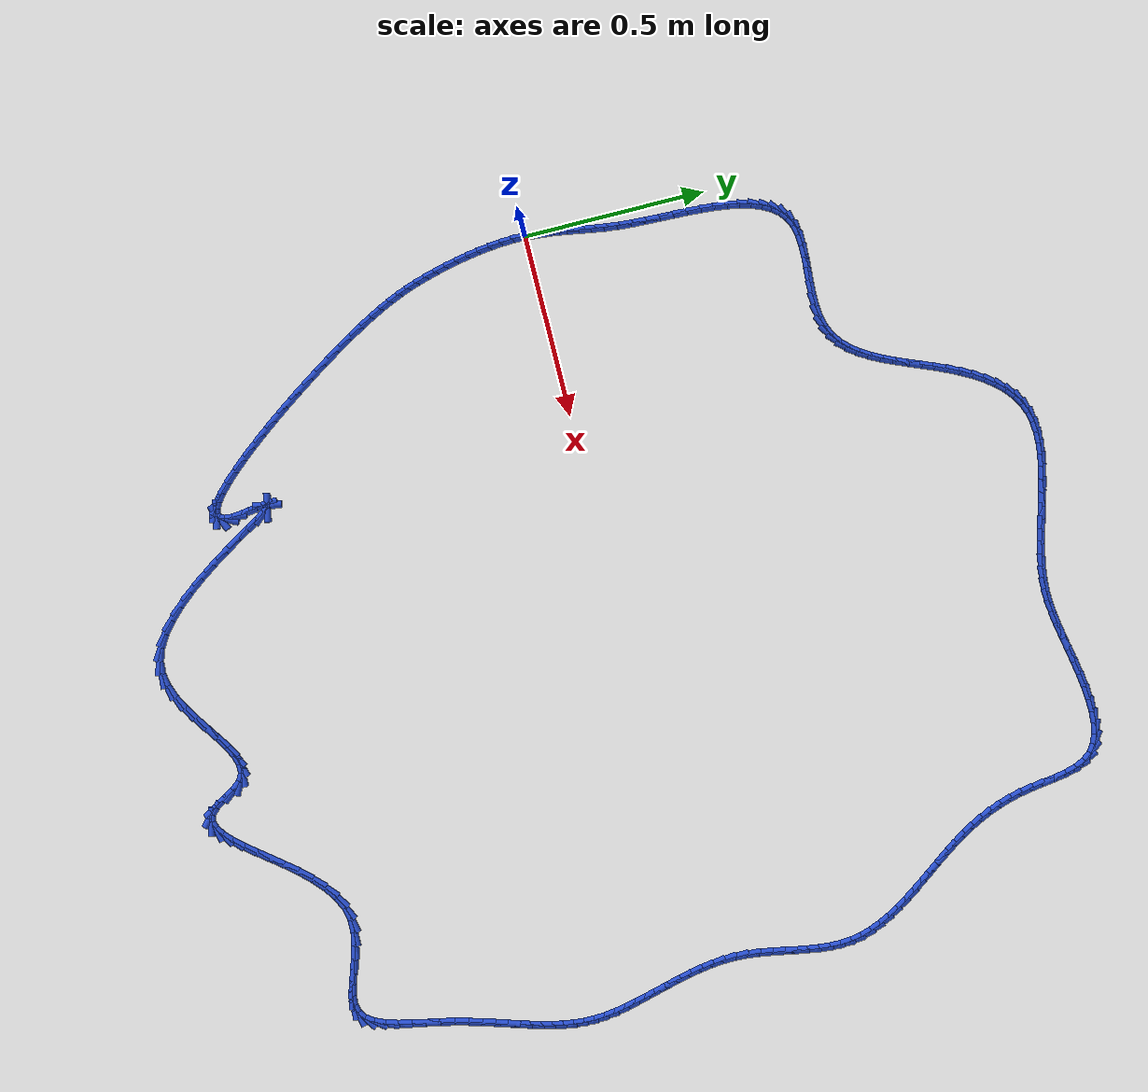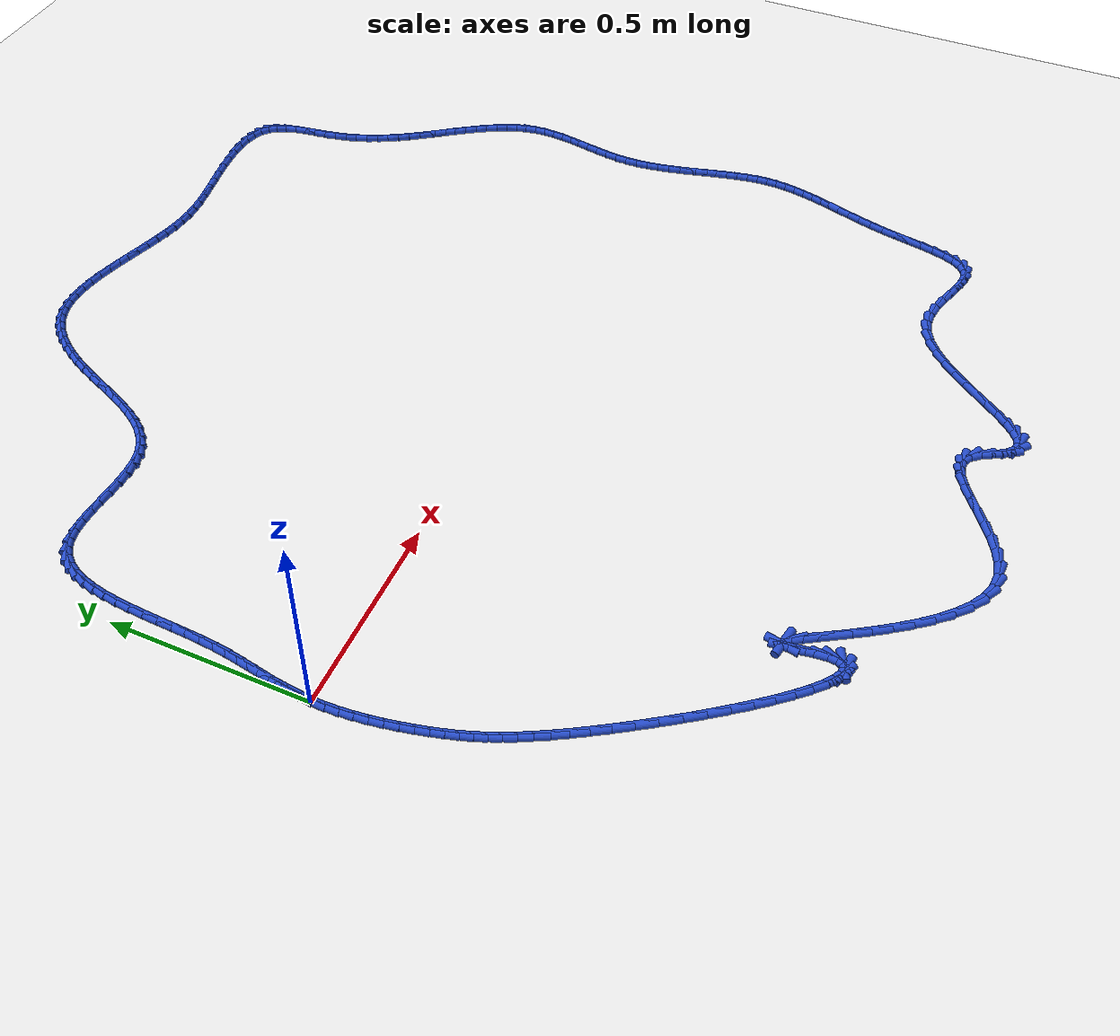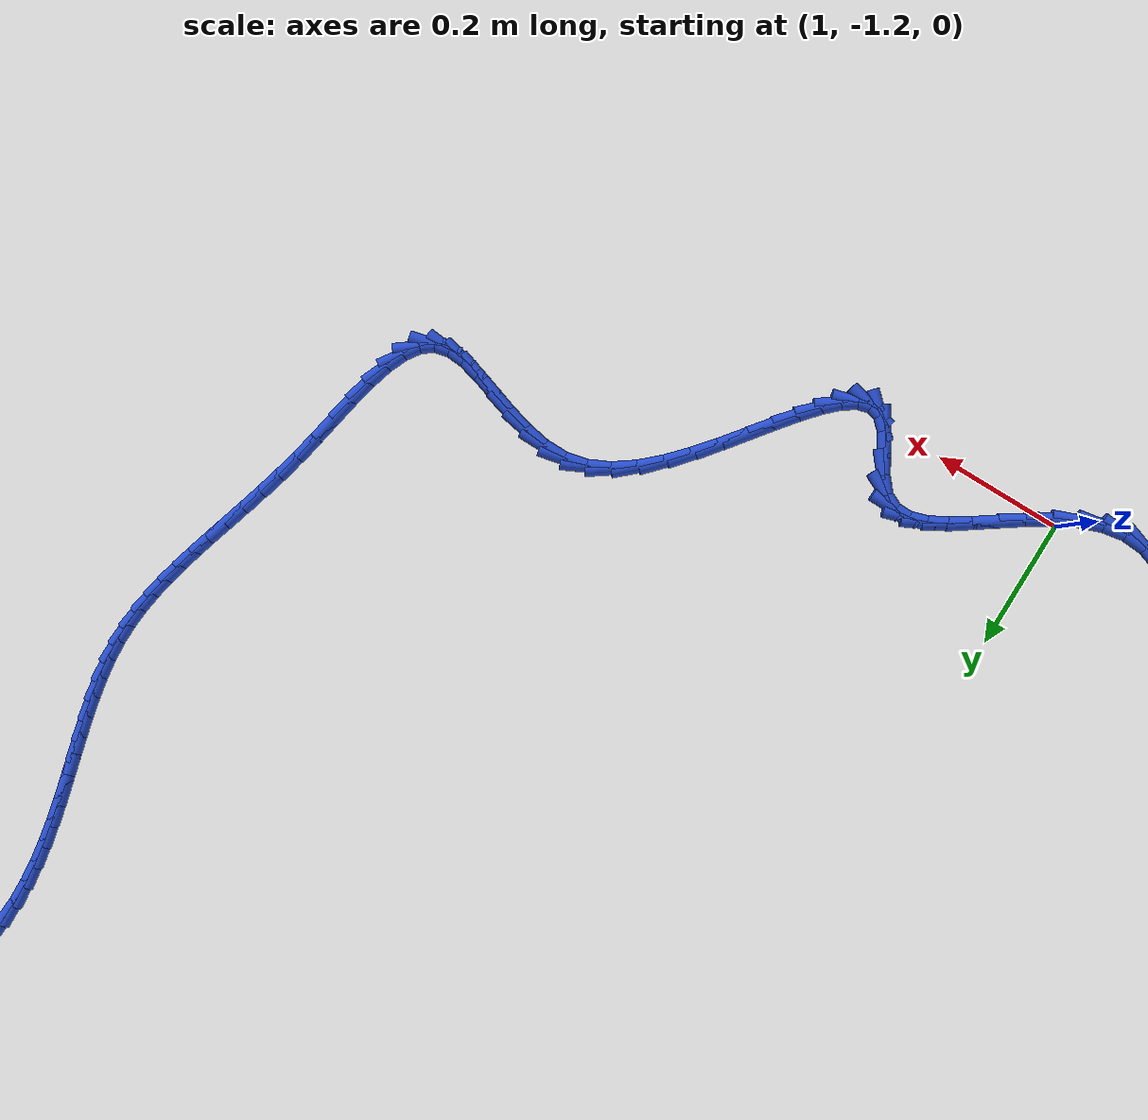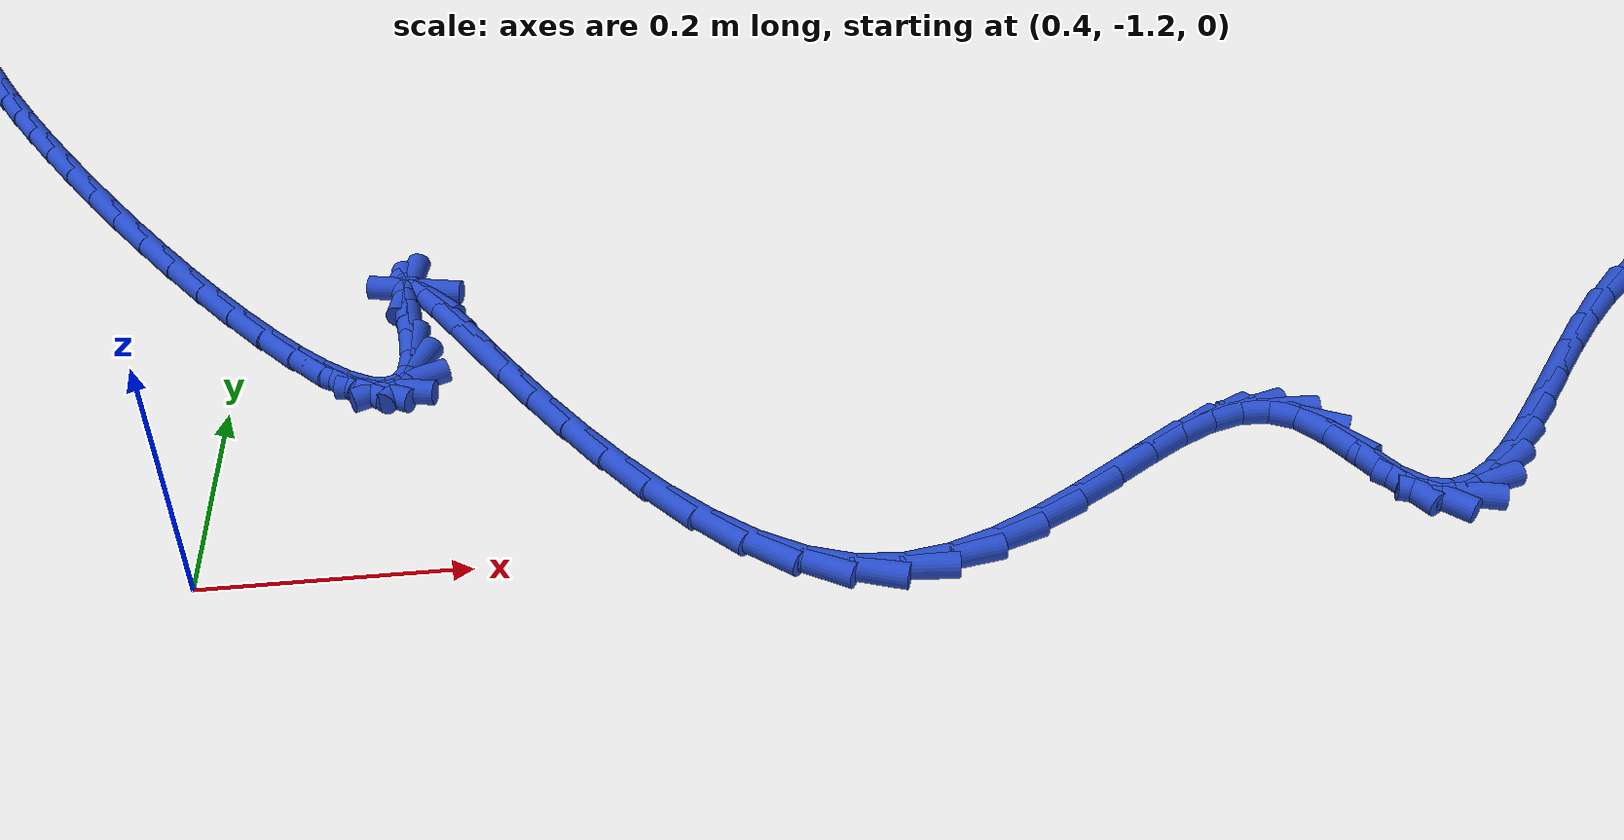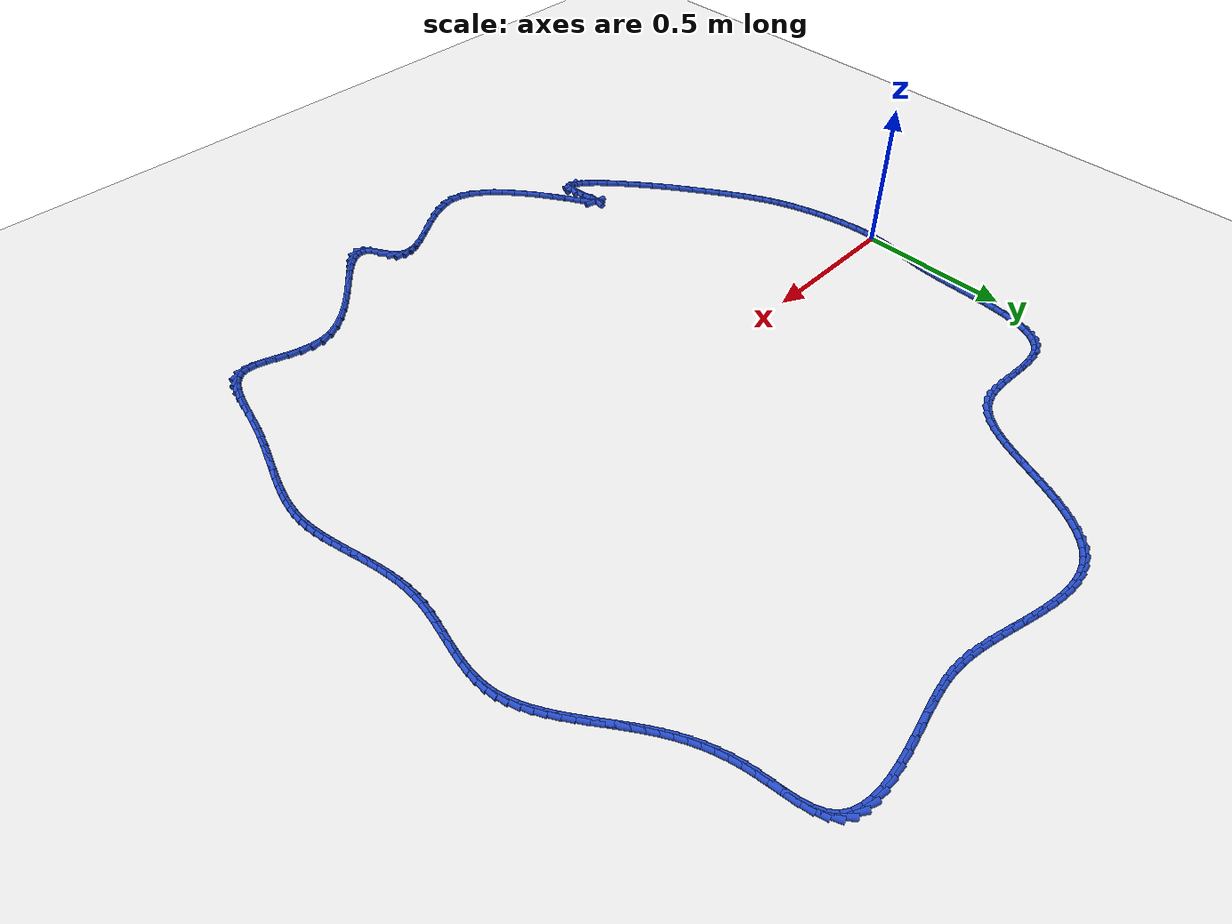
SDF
<sdf version="1.6">
 <world name="default">
  <light name="sun" type="directional">
   <pose>0 0 10 0 -0 0</pose>
   <diffuse>0.8 0.8 0.8 1</diffuse>
   <specular>0.2 0.2 0.2 1</specular>
   <attenuation>
    <range>1000</range>
    <constant>0.9</constant>
    <linear>0.01</linear>
    <quadratic>0.001</quadratic>
   </attenuation>
   <direction>-0.5 0.1 -0.9</direction>
  </light>
  <model name="ground_plane">
   <static>1</static>
   <link name="link">
    <collision name="collision">
     <geometry><plane><normal>0 0 1</normal><size>100 100</size></plane></geometry>
     <surface><friction><ode><mu>100</mu><mu2>50</mu2></ode></friction></surface>
    </collision>
    <visual name="visual">
     <cast_shadows>0</cast_shadows>
     <geometry><plane><normal>0 0 1</normal><size>100 100</size></plane></geometry>
     <material>
      <script><uri>file://media/materials/scripts/gazebo.material</uri><name>Gazebo/WhiteGlow</name></script>
     </material>
    </visual>
   </link>
  </model>
  <gravity>0 0 -9.8</gravity>
  <magnetic_field>6e-06 2.3e-05 -4.2e-05</magnetic_field>
  <atmosphere type="adiabatic"/>
  <physics name="default_physics" default="0" type="ode">
   <max_step_size>0.001</max_step_size>
   <real_time_factor>1</real_time_factor>
   <real_time_update_rate>1000</real_time_update_rate>
  </physics>
  <scene><ambient>0.4 0.4 0.4 1</ambient><background>0.7 0.7 0.7 1</background><shadows>1</shadows></scene>
  <spherical_coordinates>
   <surface_model>EARTH_WGS84</surface_model>
   <latitude_deg>0</latitude_deg>
   <longitude_deg>0</longitude_deg>
   <elevation>0</elevation>
   <heading_deg>0</heading_deg>
  </spherical_coordinates>
  <model name="line">
   <link name="link_0">
    <pose>1.5612511283791264e-17 2.7755575615628914e-17 0.01 0 1.57 1.5110017083149907</pose>
    <collision name="collision">
     <geometry><cylinder><radius>0.01</radius><length>0.08</length></cylinder></geometry>
    </collision>
    <visual name="visual">
     <material>
      <script><name>Gazebo/Blue</name><uri>file://media/materials/scripts/gazebo.material</uri></script>
     </material>
     <geometry><cylinder><radius>0.01</radius><length>0.08</length></cylinder></geometry>
    </visual>
   </link>
   <link name="link_1">
    <pose>0.0018584598975174933 0.03104367092401081 0.01 0 1.57 1.46522671874329</pose>
    <collision name="collision">
     <geometry><cylinder><radius>0.01</radius><length>0.08</length></cylinder></geometry>
    </collision>
    <visual name="visual">
     <material>
      <script><name>Gazebo/Blue</name><uri>file://media/materials/scripts/gazebo.material</uri></script>
     </material>
     <geometry><cylinder><radius>0.01</radius><length>0.08</length></cylinder></geometry>
    </visual>
   </link>
   <link name="link_2">
    <pose>0.00509891587528294 0.06162452513026185 0.01 0 1.57 1.4315644325832069</pose>
    <collision name="collision">
     <geometry><cylinder><radius>0.01</radius><length>0.08</length></cylinder></geometry>
    </collision>
    <visual name="visual">
     <material>
      <script><name>Gazebo/Blue</name><uri>file://media/materials/scripts/gazebo.material</uri></script>
     </material>
     <geometry><cylinder><radius>0.01</radius><length>0.08</length></cylinder></geometry>
    </visual>
   </link>
   <link name="link_3">
    <pose>0.009362554380947023 0.09204896133760183 0.01 0 1.57 1.4109899988886758</pose>
    <collision name="collision">
     <geometry><cylinder><radius>0.01</radius><length>0.08</length></cylinder></geometry>
    </collision>
    <visual name="visual">
     <material>
      <script><name>Gazebo/Blue</name><uri>file://media/materials/scripts/gazebo.material</uri></script>
     </material>
     <geometry><cylinder><radius>0.01</radius><length>0.08</length></cylinder></geometry>
    </visual>
   </link>
   <link name="link_4">
    <pose>0.014290561862160413 0.12262337826487943 0.01 0 1.57 1.4037116771254312</pose>
    <collision name="collision">
     <geometry><cylinder><radius>0.01</radius><length>0.08</length></cylinder></geometry>
    </collision>
    <visual name="visual">
     <material>
      <script><name>Gazebo/Blue</name><uri>file://media/materials/scripts/gazebo.material</uri></script>
     </material>
     <geometry><cylinder><radius>0.01</radius><length>0.08</length></cylinder></geometry>
    </visual>
   </link>
   <link name="link_5">
    <pose>0.019524124766573784 0.1536541746309433 0.01 0 1.57 1.40928006939681</pose>
    <collision name="collision">
     <geometry><cylinder><radius>0.01</radius><length>0.08</length></cylinder></geometry>
    </collision>
    <visual name="visual">
     <material>
      <script><name>Gazebo/Blue</name><uri>file://media/materials/scripts/gazebo.material</uri></script>
     </material>
     <geometry><cylinder><radius>0.01</radius><length>0.08</length></cylinder></geometry>
    </visual>
   </link>
   <link name="link_6">
    <pose>0.024704429541837818 0.18544774915464227 0.01 0 1.57 1.426706499615199</pose>
    <collision name="collision">
     <geometry><cylinder><radius>0.01</radius><length>0.08</length></cylinder></geometry>
    </collision>
    <visual name="visual">
     <material>
      <script><name>Gazebo/Blue</name><uri>file://media/materials/scripts/gazebo.material</uri></script>
     </material>
     <geometry><cylinder><radius>0.01</radius><length>0.08</length></cylinder></geometry>
    </visual>
   </link>
   <link name="link_7">
    <pose>0.02947266263560318 0.21831050055482487 0.01 0 1.57 1.4545718183914698</pose>
    <collision name="collision">
     <geometry><cylinder><radius>0.01</radius><length>0.08</length></cylinder></geometry>
    </collision>
    <visual name="visual">
     <material>
      <script><name>Gazebo/Blue</name><uri>file://media/materials/scripts/gazebo.material</uri></script>
     </material>
     <geometry><cylinder><radius>0.01</radius><length>0.08</length></cylinder></geometry>
    </visual>
   </link>
   <link name="link_8">
    <pose>0.03347001049552052 0.25254882755033975 0.01 0 1.57 1.4891182606874604</pose>
    <collision name="collision">
     <geometry><cylinder><radius>0.01</radius><length>0.08</length></cylinder></geometry>
    </collision>
    <visual name="visual">
     <material>
      <script><name>Gazebo/Blue</name><uri>file://media/materials/scripts/gazebo.material</uri></script>
     </material>
     <geometry><cylinder><radius>0.01</radius><length>0.08</length></cylinder></geometry>
    </visual>
   </link>
   <link name="link_9">
    <pose>0.03640450453529545 0.288396462525026 0.01 0 1.57 1.5159817689432553</pose>
    <collision name="collision">
     <geometry><cylinder><radius>0.01</radius><length>0.08</length></cylinder></geometry>
    </collision>
    <visual name="visual">
     <material>
      <script><name>Gazebo/Blue</name><uri>file://media/materials/scripts/gazebo.material</uri></script>
     </material>
     <geometry><cylinder><radius>0.01</radius><length>0.08</length></cylinder></geometry>
    </visual>
   </link>
   <link name="link_10">
    <pose>0.03844508182791089 0.3255860930268645 0.01 0 1.57 1.5311385465173644</pose>
    <collision name="collision">
     <geometry><cylinder><radius>0.01</radius><length>0.08</length></cylinder></geometry>
    </collision>
    <visual name="visual">
     <material>
      <script><name>Gazebo/Blue</name><uri>file://media/materials/scripts/gazebo.material</uri></script>
     </material>
     <geometry><cylinder><radius>0.01</radius><length>0.08</length></cylinder></geometry>
    </visual>
   </link>
   <link name="link_11">
    <pose>0.03995497484480821 0.3636391904816875 0.01 0 1.57 1.535867308461193</pose>
    <collision name="collision">
     <geometry><cylinder><radius>0.01</radius><length>0.08</length></cylinder></geometry>
    </collision>
    <visual name="visual">
     <material>
      <script><name>Gazebo/Blue</name><uri>file://media/materials/scripts/gazebo.material</uri></script>
     </material>
     <geometry><cylinder><radius>0.01</radius><length>0.08</length></cylinder></geometry>
    </visual>
   </link>
   <link name="link_12">
    <pose>0.04129809807063453 0.40207648490721637 0.01 0 1.57 1.5306463270078754</pose>
    <collision name="collision">
     <geometry><cylinder><radius>0.01</radius><length>0.08</length></cylinder></geometry>
    </collision>
    <visual name="visual">
     <material>
      <script><name>Gazebo/Blue</name><uri>file://media/materials/scripts/gazebo.material</uri></script>
     </material>
     <geometry><cylinder><radius>0.01</radius><length>0.08</length></cylinder></geometry>
    </visual>
   </link>
   <link name="link_13">
    <pose>0.04283836599003689 0.4404187063211712 0.01 0 1.57 1.5152156871650295</pose>
    <collision name="collision">
     <geometry><cylinder><radius>0.01</radius><length>0.08</length></cylinder></geometry>
    </collision>
    <visual name="visual">
     <material>
      <script><name>Gazebo/Blue</name><uri>file://media/materials/scripts/gazebo.material</uri></script>
     </material>
     <geometry><cylinder><radius>0.01</radius><length>0.08</length></cylinder></geometry>
    </visual>
   </link>
   <link name="link_14">
    <pose>0.0449396930876624 0.4781865847412729 0.01 0 1.57 1.4885537839730054</pose>
    <collision name="collision">
     <geometry><cylinder><radius>0.01</radius><length>0.08</length></cylinder></geometry>
    </collision>
    <visual name="visual">
     <material>
      <script><name>Gazebo/Blue</name><uri>file://media/materials/scripts/gazebo.material</uri></script>
     </material>
     <geometry><cylinder><radius>0.01</radius><length>0.08</length></cylinder></geometry>
    </visual>
   </link>
   <link name="link_15">
    <pose>0.04796599384815814 0.5149008501852421 0.01 0 1.57 1.4487504574559473</pose>
    <collision name="collision">
     <geometry><cylinder><radius>0.01</radius><length>0.08</length></cylinder></geometry>
    </collision>
    <visual name="visual">
     <material>
      <script><name>Gazebo/Blue</name><uri>file://media/materials/scripts/gazebo.material</uri></script>
     </material>
     <geometry><cylinder><radius>0.01</radius><length>0.08</length></cylinder></geometry>
    </visual>
   </link>
   <link name="link_16">
    <pose>0.05228118275617119 0.5500822326707997 0.01 0 1.57 1.392775512622296</pose>
    <collision name="collision">
     <geometry><cylinder><radius>0.01</radius><length>0.08</length></cylinder></geometry>
    </collision>
    <visual name="visual">
     <material>
      <script><name>Gazebo/Blue</name><uri>file://media/materials/scripts/gazebo.material</uri></script>
     </material>
     <geometry><cylinder><radius>0.01</radius><length>0.08</length></cylinder></geometry>
    </visual>
   </link>
   <link name="link_17">
    <pose>0.05824917429634862 0.5832514622156658 0.01 0 1.57 1.316169399740432</pose>
    <collision name="collision">
     <geometry><cylinder><radius>0.01</radius><length>0.08</length></cylinder></geometry>
    </collision>
    <visual name="visual">
     <material>
      <script><name>Gazebo/Blue</name><uri>file://media/materials/scripts/gazebo.material</uri></script>
     </material>
     <geometry><cylinder><radius>0.01</radius><length>0.08</length></cylinder></geometry>
    </visual>
   </link>
   <link name="link_18">
    <pose>0.06623388295333751 0.6139292688375618 0.01 0 1.57 1.2128114794268512</pose>
    <collision name="collision">
     <geometry><cylinder><radius>0.01</radius><length>0.08</length></cylinder></geometry>
    </collision>
    <visual name="visual">
     <material>
      <script><name>Gazebo/Blue</name><uri>file://media/materials/scripts/gazebo.material</uri></script>
     </material>
     <geometry><cylinder><radius>0.01</radius><length>0.08</length></cylinder></geometry>
    </visual>
   </link>
   <link name="link_19">
    <pose>0.07659922321178494 0.6416363825542076 0.01 0 1.57 1.075311240369714</pose>
    <collision name="collision">
     <geometry><cylinder><radius>0.01</radius><length>0.08</length></cylinder></geometry>
    </collision>
    <visual name="visual">
     <material>
      <script><name>Gazebo/Blue</name><uri>file://media/materials/scripts/gazebo.material</uri></script>
     </material>
     <geometry><cylinder><radius>0.01</radius><length>0.08</length></cylinder></geometry>
    </visual>
   </link>
   <link name="link_20">
    <pose>0.08970910955633804 0.6658935333833244 0.01 0 1.57 0.8973762253620209</pose>
    <collision name="collision">
     <geometry><cylinder><radius>0.01</radius><length>0.08</length></cylinder></geometry>
    </collision>
    <visual name="visual">
     <material>
      <script><name>Gazebo/Blue</name><uri>file://media/materials/scripts/gazebo.material</uri></script>
     </material>
     <geometry><cylinder><radius>0.01</radius><length>0.08</length></cylinder></geometry>
    </visual>
   </link>
   <link name="link_21">
    <pose>0.10592745647164384 0.686221451342633 0.01 0 1.57 0.6798860341663364</pose>
    <collision name="collision">
     <geometry><cylinder><radius>0.01</radius><length>0.08</length></cylinder></geometry>
    </collision>
    <visual name="visual">
     <material>
      <script><name>Gazebo/Blue</name><uri>file://media/materials/scripts/gazebo.material</uri></script>
     </material>
     <geometry><cylinder><radius>0.01</radius><length>0.08</length></cylinder></geometry>
    </visual>
   </link>
   <link name="link_22">
    <pose>0.12561817844234943 0.7021408664498535 0.01 0 1.57 0.43867159131562394</pose>
    <collision name="collision">
     <geometry><cylinder><radius>0.01</radius><length>0.08</length></cylinder></geometry>
    </collision>
    <visual name="visual">
     <material>
      <script><name>Gazebo/Blue</name><uri>file://media/materials/scripts/gazebo.material</uri></script>
     </material>
     <geometry><cylinder><radius>0.01</radius><length>0.08</length></cylinder></geometry>
    </visual>
   </link>
   <link name="link_23">
    <pose>0.14914177529060485 0.7131771668245567 0.01 0 1.57 0.222887089520099</pose>
    <collision name="collision">
     <geometry><cylinder><radius>0.01</radius><length>0.08</length></cylinder></geometry>
    </collision>
    <visual name="visual">
     <material>
      <script><name>Gazebo/Blue</name><uri>file://media/materials/scripts/gazebo.material</uri></script>
     </material>
     <geometry><cylinder><radius>0.01</radius><length>0.08</length></cylinder></geometry>
    </visual>
   </link>
   <link name="link_24">
    <pose>0.1764793422462872 0.7193733042502569 0.01 0 1.57 0.07810402708663557</pose>
    <collision name="collision">
     <geometry><cylinder><radius>0.01</radius><length>0.08</length></cylinder></geometry>
    </collision>
    <visual name="visual">
     <material>
      <script><name>Gazebo/Blue</name><uri>file://media/materials/scripts/gazebo.material</uri></script>
     </material>
     <geometry><cylinder><radius>0.01</radius><length>0.08</length></cylinder></geometry>
    </visual>
   </link>
   <link name="link_25">
    <pose>0.20689261320327226 0.721753545171237 0.01 0 1.57 -0.009240623474178342</pose>
    <collision name="collision">
     <geometry><cylinder><radius>0.01</radius><length>0.08</length></cylinder></geometry>
    </collision>
    <visual name="visual">
     <material>
      <script><name>Gazebo/Blue</name><uri>file://media/materials/scripts/gazebo.material</uri></script>
     </material>
     <geometry><cylinder><radius>0.01</radius><length>0.08</length></cylinder></geometry>
    </visual>
   </link>
   <link name="link_26">
    <pose>0.23956306295168178 0.7214516412532275 0.01 0 1.57 -0.05419331402597103</pose>
    <collision name="collision">
     <geometry><cylinder><radius>0.01</radius><length>0.08</length></cylinder></geometry>
    </collision>
    <visual name="visual">
     <material>
      <script><name>Gazebo/Blue</name><uri>file://media/materials/scripts/gazebo.material</uri></script>
     </material>
     <geometry><cylinder><radius>0.01</radius><length>0.08</length></cylinder></geometry>
    </visual>
   </link>
   <link name="link_27">
    <pose>0.2736721662816378 0.7196013441619609 0.01 0 1.57 -0.06512483948747246</pose>
    <collision name="collision">
     <geometry><cylinder><radius>0.01</radius><length>0.08</length></cylinder></geometry>
    </collision>
    <visual name="visual">
     <material>
      <script><name>Gazebo/Blue</name><uri>file://media/materials/scripts/gazebo.material</uri></script>
     </material>
     <geometry><cylinder><radius>0.01</radius><length>0.08</length></cylinder></geometry>
    </visual>
   </link>
   <link name="link_28">
    <pose>0.3084013979832621 0.7173364055631677 0.01 0 1.57 -0.044736741747783436</pose>
    <collision name="collision">
     <geometry><cylinder><radius>0.01</radius><length>0.08</length></cylinder></geometry>
    </collision>
    <visual name="visual">
     <material>
      <script><name>Gazebo/Blue</name><uri>file://media/materials/scripts/gazebo.material</uri></script>
     </material>
     <geometry><cylinder><radius>0.01</radius><length>0.08</length></cylinder></geometry>
    </visual>
   </link>
   <link name="link_29">
    <pose>0.34293223284667657 0.7157905771225797 0.01 0 1.57 0.009161114538576076</pose>
    <collision name="collision">
     <geometry><cylinder><radius>0.01</radius><length>0.08</length></cylinder></geometry>
    </collision>
    <visual name="visual">
     <material>
      <script><name>Gazebo/Blue</name><uri>file://media/materials/scripts/gazebo.material</uri></script>
     </material>
     <geometry><cylinder><radius>0.01</radius><length>0.08</length></cylinder></geometry>
    </visual>
   </link>
   <link name="link_30">
    <pose>0.376446145662003 0.716097610505928 0.01 0 1.57 0.1035989304440568</pose>
    <collision name="collision">
     <geometry><cylinder><radius>0.01</radius><length>0.08</length></cylinder></geometry>
    </collision>
    <visual name="visual">
     <material>
      <script><name>Gazebo/Blue</name><uri>file://media/materials/scripts/gazebo.material</uri></script>
     </material>
     <geometry><cylinder><radius>0.01</radius><length>0.08</length></cylinder></geometry>
    </visual>
   </link>
   <link name="link_31">
    <pose>0.4081246112193635 0.7193912573789447 0.01 0 1.57 0.2500420094478546</pose>
    <collision name="collision">
     <geometry><cylinder><radius>0.01</radius><length>0.08</length></cylinder></geometry>
    </collision>
    <visual name="visual">
     <material>
      <script><name>Gazebo/Blue</name><uri>file://media/materials/scripts/gazebo.material</uri></script>
     </material>
     <geometry><cylinder><radius>0.01</radius><length>0.08</length></cylinder></geometry>
    </visual>
   </link>
   <link name="link_32">
    <pose>0.43715005025850145 0.7268039676046116 0.01 0 1.57 0.44155622837616293</pose>
    <collision name="collision">
     <geometry><cylinder><radius>0.01</radius><length>0.08</length></cylinder></geometry>
    </collision>
    <visual name="visual">
     <material>
      <script><name>Gazebo/Blue</name><uri>file://media/materials/scripts/gazebo.material</uri></script>
     </material>
     <geometry><cylinder><radius>0.01</radius><length>0.08</length></cylinder></geometry>
    </visual>
   </link>
   <link name="link_33">
    <pose>0.463021231771554 0.7390328369686503 0.01 0 1.57 0.6276039159924935</pose>
    <collision name="collision">
     <geometry><cylinder><radius>0.01</radius><length>0.08</length></cylinder></geometry>
    </collision>
    <visual name="visual">
     <material>
      <script><name>Gazebo/Blue</name><uri>file://media/materials/scripts/gazebo.material</uri></script>
     </material>
     <geometry><cylinder><radius>0.01</radius><length>0.08</length></cylinder></geometry>
    </visual>
   </link>
   <link name="link_34">
    <pose>0.48601047485320986 0.7557104123346278 0.01 0 1.57 0.7879160891610285</pose>
    <collision name="collision">
     <geometry><cylinder><radius>0.01</radius><length>0.08</length></cylinder></geometry>
    </collision>
    <visual name="visual">
     <material>
      <script><name>Gazebo/Blue</name><uri>file://media/materials/scripts/gazebo.material</uri></script>
     </material>
     <geometry><cylinder><radius>0.01</radius><length>0.08</length></cylinder></geometry>
    </visual>
   </link>
   <link name="link_35">
    <pose>0.5065061377457422 0.7763095491006426 0.01 0 1.57 0.91683480049951</pose>
    <collision name="collision">
     <geometry><cylinder><radius>0.01</radius><length>0.08</length></cylinder></geometry>
    </collision>
    <visual name="visual">
     <material>
      <script><name>Gazebo/Blue</name><uri>file://media/materials/scripts/gazebo.material</uri></script>
     </material>
     <geometry><cylinder><radius>0.01</radius><length>0.08</length></cylinder></geometry>
    </visual>
   </link>
   <link name="link_36">
    <pose>0.5248965786914249 0.8003031026647943 0.01 0 1.57 1.015266564539035</pose>
    <collision name="collision">
     <geometry><cylinder><radius>0.01</radius><length>0.08</length></cylinder></geometry>
    </collision>
    <visual name="visual">
     <material>
      <script><name>Gazebo/Blue</name><uri>file://media/materials/scripts/gazebo.material</uri></script>
     </material>
     <geometry><cylinder><radius>0.01</radius><length>0.08</length></cylinder></geometry>
    </visual>
   </link>
   <link name="link_37">
    <pose>0.5415701559325311 0.827163928425182 0.01 0 1.57 1.0869582249928893</pose>
    <collision name="collision">
     <geometry><cylinder><radius>0.01</radius><length>0.08</length></cylinder></geometry>
    </collision>
    <visual name="visual">
     <material>
      <script><name>Gazebo/Blue</name><uri>file://media/materials/scripts/gazebo.material</uri></script>
     </material>
     <geometry><cylinder><radius>0.01</radius><length>0.08</length></cylinder></geometry>
    </visual>
   </link>
   <link name="link_38">
    <pose>0.5569152277113344 0.8563648817799047 0.01 0 1.57 1.13597765855752</pose>
    <collision name="collision">
     <geometry><cylinder><radius>0.01</radius><length>0.08</length></cylinder></geometry>
    </collision>
    <visual name="visual">
     <material>
      <script><name>Gazebo/Blue</name><uri>file://media/materials/scripts/gazebo.material</uri></script>
     </material>
     <geometry><cylinder><radius>0.01</radius><length>0.08</length></cylinder></geometry>
    </visual>
   </link>
   <link name="link_39">
    <pose>0.5713201522701081 0.8873788181270611 0.01 0 1.57 1.1656332058274104</pose>
    <collision name="collision">
     <geometry><cylinder><radius>0.01</radius><length>0.08</length></cylinder></geometry>
    </collision>
    <visual name="visual">
     <material>
      <script><name>Gazebo/Blue</name><uri>file://media/materials/scripts/gazebo.material</uri></script>
     </material>
     <geometry><cylinder><radius>0.01</radius><length>0.08</length></cylinder></geometry>
    </visual>
   </link>
   <link name="link_40">
    <pose>0.5851732878511255 0.9196785928647508 0.01 0 1.57 1.1781891962383126</pose>
    <collision name="collision">
     <geometry><cylinder><radius>0.01</radius><length>0.08</length></cylinder></geometry>
    </collision>
    <visual name="visual">
     <material>
      <script><name>Gazebo/Blue</name><uri>file://media/materials/scripts/gazebo.material</uri></script>
     </material>
     <geometry><cylinder><radius>0.01</radius><length>0.08</length></cylinder></geometry>
    </visual>
   </link>
   <link name="link_41">
    <pose>0.5988629926966605 0.952737061391073 0.01 0 1.57 1.1748848666998863</pose>
    <collision name="collision">
     <geometry><cylinder><radius>0.01</radius><length>0.08</length></cylinder></geometry>
    </collision>
    <visual name="visual">
     <material>
      <script><name>Gazebo/Blue</name><uri>file://media/materials/scripts/gazebo.material</uri></script>
     </material>
     <geometry><cylinder><radius>0.01</radius><length>0.08</length></cylinder></geometry>
    </visual>
   </link>
   <link name="link_42">
    <pose>0.6127776250489861 0.9860270791041266 0.01 0 1.57 1.1560261072629114</pose>
    <collision name="collision">
     <geometry><cylinder><radius>0.01</radius><length>0.08</length></cylinder></geometry>
    </collision>
    <visual name="visual">
     <material>
      <script><name>Gazebo/Blue</name><uri>file://media/materials/scripts/gazebo.material</uri></script>
     </material>
     <geometry><cylinder><radius>0.01</radius><length>0.08</length></cylinder></geometry>
    </visual>
   </link>
   <link name="link_43">
    <pose>0.627305543150376 1.0190215014020108 0.01 0 1.57 1.1210769184691094</pose>
    <collision name="collision">
     <geometry><cylinder><radius>0.01</radius><length>0.08</length></cylinder></geometry>
    </collision>
    <visual name="visual">
     <material>
      <script><name>Gazebo/Blue</name><uri>file://media/materials/scripts/gazebo.material</uri></script>
     </material>
     <geometry><cylinder><radius>0.01</radius><length>0.08</length></cylinder></geometry>
    </visual>
   </link>
   <link name="link_44">
    <pose>0.6428351052431033 1.051193183682824 0.01 0 1.57 1.0695364520800479</pose>
    <collision name="collision">
     <geometry><cylinder><radius>0.01</radius><length>0.08</length></cylinder></geometry>
    </collision>
    <visual name="visual">
     <material>
      <script><name>Gazebo/Blue</name><uri>file://media/materials/scripts/gazebo.material</uri></script>
     </material>
     <geometry><cylinder><radius>0.01</radius><length>0.08</length></cylinder></geometry>
    </visual>
   </link>
   <link name="link_45">
    <pose>0.6597184352597053 1.0820055819536332 0.01 0 1.57 1.0039581526693369</pose>
    <collision name="collision">
     <geometry><cylinder><radius>0.01</radius><length>0.08</length></cylinder></geometry>
    </collision>
    <visual name="visual">
     <material>
      <script><name>Gazebo/Blue</name><uri>file://media/materials/scripts/gazebo.material</uri></script>
     </material>
     <geometry><cylinder><radius>0.01</radius><length>0.08</length></cylinder></geometry>
    </visual>
   </link>
   <link name="link_46">
    <pose>0.678088056257983 1.1108651864752859 0.01 0 1.57 0.9227545385872424</pose>
    <collision name="collision">
     <geometry><cylinder><radius>0.01</radius><length>0.08</length></cylinder></geometry>
    </collision>
    <visual name="visual">
     <material>
      <script><name>Gazebo/Blue</name><uri>file://media/materials/scripts/gazebo.material</uri></script>
     </material>
     <geometry><cylinder><radius>0.01</radius><length>0.08</length></cylinder></geometry>
    </visual>
   </link>
   <link name="link_47">
    <pose>0.6979941963617103 1.1371571397233247 0.01 0 1.57 0.8216286395048461</pose>
    <collision name="collision">
     <geometry><cylinder><radius>0.01</radius><length>0.08</length></cylinder></geometry>
    </collision>
    <visual name="visual">
     <material>
      <script><name>Gazebo/Blue</name><uri>file://media/materials/scripts/gazebo.material</uri></script>
     </material>
     <geometry><cylinder><radius>0.01</radius><length>0.08</length></cylinder></geometry>
    </visual>
   </link>
   <link name="link_48">
    <pose>0.7194869386581428 1.1602665465499726 0.01 0 1.57 0.6956928824648573</pose>
    <collision name="collision">
     <geometry><cylinder><radius>0.01</radius><length>0.08</length></cylinder></geometry>
    </collision>
    <visual name="visual">
     <material>
      <script><name>Gazebo/Blue</name><uri>file://media/materials/scripts/gazebo.material</uri></script>
     </material>
     <geometry><cylinder><radius>0.01</radius><length>0.08</length></cylinder></geometry>
    </visual>
   </link>
   <link name="link_49">
    <pose>0.7426163662345364 1.1795785118074549 0.01 0 1.57 0.5410460445097256</pose>
    <collision name="collision">
     <geometry><cylinder><radius>0.01</radius><length>0.08</length></cylinder></geometry>
    </collision>
    <visual name="visual">
     <material>
      <script><name>Gazebo/Blue</name><uri>file://media/materials/scripts/gazebo.material</uri></script>
     </material>
     <geometry><cylinder><radius>0.01</radius><length>0.08</length></cylinder></geometry>
    </visual>
   </link>
   <link name="link_50">
    <pose>0.7674305798383994 1.194488192119707 0.01 0 1.57 0.372577959626737</pose>
    <collision name="collision">
     <geometry><cylinder><radius>0.01</radius><length>0.08</length></cylinder></geometry>
    </collision>
    <visual name="visual">
     <material>
      <script><name>Gazebo/Blue</name><uri>file://media/materials/scripts/gazebo.material</uri></script>
     </material>
     <geometry><cylinder><radius>0.01</radius><length>0.08</length></cylinder></geometry>
    </visual>
   </link>
   <link name="link_51">
    <pose>0.7938910917605801 1.2048298047710282 0.01 0 1.57 0.21855425497329292</pose>
    <collision name="collision">
     <geometry><cylinder><radius>0.01</radius><length>0.08</length></cylinder></geometry>
    </collision>
    <visual name="visual">
     <material>
      <script><name>Gazebo/Blue</name><uri>file://media/materials/scripts/gazebo.material</uri></script>
     </material>
     <geometry><cylinder><radius>0.01</radius><length>0.08</length></cylinder></geometry>
    </visual>
   </link>
   <link name="link_52">
    <pose>0.8218410895627285 1.2110375515672762 0.01 0 1.57 0.08693254520243908</pose>
    <collision name="collision">
     <geometry><cylinder><radius>0.01</radius><length>0.08</length></cylinder></geometry>
    </collision>
    <visual name="visual">
     <material>
      <script><name>Gazebo/Blue</name><uri>file://media/materials/scripts/gazebo.material</uri></script>
     </material>
     <geometry><cylinder><radius>0.01</radius><length>0.08</length></cylinder></geometry>
    </visual>
   </link>
   <link name="link_53">
    <pose>0.8511152365582317 1.2135888578826068 0.01 0 1.57 -0.02062302875035609</pose>
    <collision name="collision">
     <geometry><cylinder><radius>0.01</radius><length>0.08</length></cylinder></geometry>
    </collision>
    <visual name="visual">
     <material>
      <script><name>Gazebo/Blue</name><uri>file://media/materials/scripts/gazebo.material</uri></script>
     </material>
     <geometry><cylinder><radius>0.01</radius><length>0.08</length></cylinder></geometry>
    </visual>
   </link>
   <link name="link_54">
    <pose>0.8815481960604791 1.2129611490911782 0.01 0 1.57 -0.10554574863978079</pose>
    <collision name="collision">
     <geometry><cylinder><radius>0.01</radius><length>0.08</length></cylinder></geometry>
    </collision>
    <visual name="visual">
     <material>
      <script><name>Gazebo/Blue</name><uri>file://media/materials/scripts/gazebo.material</uri></script>
     </material>
     <geometry><cylinder><radius>0.01</radius><length>0.08</length></cylinder></geometry>
    </visual>
   </link>
   <link name="link_55">
    <pose>0.9129746313828582 1.2096318505671468 0.01 0 1.57 -0.17050425192611332</pose>
    <collision name="collision">
     <geometry><cylinder><radius>0.01</radius><length>0.08</length></cylinder></geometry>
    </collision>
    <visual name="visual">
     <material>
      <script><name>Gazebo/Blue</name><uri>file://media/materials/scripts/gazebo.material</uri></script>
     </material>
     <geometry><cylinder><radius>0.01</radius><length>0.08</length></cylinder></geometry>
    </visual>
   </link>
   <link name="link_56">
    <pose>0.9452292058387579 1.2040783876846692 0.01 0 1.57 -0.2182412988082091</pose>
    <collision name="collision">
     <geometry><cylinder><radius>0.01</radius><length>0.08</length></cylinder></geometry>
    </collision>
    <visual name="visual">
     <material>
      <script><name>Gazebo/Blue</name><uri>file://media/materials/scripts/gazebo.material</uri></script>
     </material>
     <geometry><cylinder><radius>0.01</radius><length>0.08</length></cylinder></geometry>
    </visual>
   </link>
   <link name="link_57">
    <pose>0.9781465827415662 1.1967781858179025 0.01 0 1.57 -0.2510478145431154</pose>
    <collision name="collision">
     <geometry><cylinder><radius>0.01</radius><length>0.08</length></cylinder></geometry>
    </collision>
    <visual name="visual">
     <material>
      <script><name>Gazebo/Blue</name><uri>file://media/materials/scripts/gazebo.material</uri></script>
     </material>
     <geometry><cylinder><radius>0.01</radius><length>0.08</length></cylinder></geometry>
    </visual>
   </link>
   <link name="link_58">
    <pose>1.0115614254046716 1.1882086703410042 0.01 0 1.57 -0.2705959279661808</pose>
    <collision name="collision">
     <geometry><cylinder><radius>0.01</radius><length>0.08</length></cylinder></geometry>
    </collision>
    <visual name="visual">
     <material>
      <script><name>Gazebo/Blue</name><uri>file://media/materials/scripts/gazebo.material</uri></script>
     </material>
     <geometry><cylinder><radius>0.01</radius><length>0.08</length></cylinder></geometry>
    </visual>
   </link>
   <link name="link_59">
    <pose>1.045308397141462 1.17884726662813 0.01 0 1.57 -0.2779239513480652</pose>
    <collision name="collision">
     <geometry><cylinder><radius>0.01</radius><length>0.08</length></cylinder></geometry>
    </collision>
    <visual name="visual">
     <material>
      <script><name>Gazebo/Blue</name><uri>file://media/materials/scripts/gazebo.material</uri></script>
     </material>
     <geometry><cylinder><radius>0.01</radius><length>0.08</length></cylinder></geometry>
    </visual>
   </link>
   <link name="link_60">
    <pose>1.0792221612653266 1.169171400053438 0.01 0 1.57 -0.273463679614006</pose>
    <collision name="collision">
     <geometry><cylinder><radius>0.01</radius><length>0.08</length></cylinder></geometry>
    </collision>
    <visual name="visual">
     <material>
      <script><name>Gazebo/Blue</name><uri>file://media/materials/scripts/gazebo.material</uri></script>
     </material>
     <geometry><cylinder><radius>0.01</radius><length>0.08</length></cylinder></geometry>
    </visual>
   </link>
   <link name="link_61">
    <pose>1.1131373810896528 1.1596584959910847 0.01 0 1.57 -0.25706280930276276</pose>
    <collision name="collision">
     <geometry><cylinder><radius>0.01</radius><length>0.08</length></cylinder></geometry>
    </collision>
    <visual name="visual">
     <material>
      <script><name>Gazebo/Blue</name><uri>file://media/materials/scripts/gazebo.material</uri></script>
     </material>
     <geometry><cylinder><radius>0.01</radius><length>0.08</length></cylinder></geometry>
    </visual>
   </link>
   <link name="link_62">
    <pose>1.1468887199278295 1.150785979815227 0.01 0 1.57 -0.22798895649781153</pose>
    <collision name="collision">
     <geometry><cylinder><radius>0.01</radius><length>0.08</length></cylinder></geometry>
    </collision>
    <visual name="visual">
     <material>
      <script><name>Gazebo/Blue</name><uri>file://media/materials/scripts/gazebo.material</uri></script>
     </material>
     <geometry><cylinder><radius>0.01</radius><length>0.08</length></cylinder></geometry>
    </visual>
   </link>
   <link name="link_63">
    <pose>1.1803108410932448 1.1430312769000215 0.01 0 1.57 -0.18492384644877874</pose>
    <collision name="collision">
     <geometry><cylinder><radius>0.01</radius><length>0.08</length></cylinder></geometry>
    </collision>
    <visual name="visual">
     <material>
      <script><name>Gazebo/Blue</name><uri>file://media/materials/scripts/gazebo.material</uri></script>
     </material>
     <geometry><cylinder><radius>0.01</radius><length>0.08</length></cylinder></geometry>
    </visual>
   </link>
   <link name="link_64">
    <pose>1.2132384078992868 1.1368718126196256 0.01 0 1.57 -0.1259823024578355</pose>
    <collision name="collision">
     <geometry><cylinder><radius>0.01</radius><length>0.08</length></cylinder></geometry>
    </collision>
    <visual name="visual">
     <material>
      <script><name>Gazebo/Blue</name><uri>file://media/materials/scripts/gazebo.material</uri></script>
     </material>
     <geometry><cylinder><radius>0.01</radius><length>0.08</length></cylinder></geometry>
    </visual>
   </link>
   <link name="link_65">
    <pose>1.2455060836593446 1.132785012348196 0.01 0 1.57 -0.05015618788711209</pose>
    <collision name="collision">
     <geometry><cylinder><radius>0.01</radius><length>0.08</length></cylinder></geometry>
    </collision>
    <visual name="visual">
     <material>
      <script><name>Gazebo/Blue</name><uri>file://media/materials/scripts/gazebo.material</uri></script>
     </material>
     <geometry><cylinder><radius>0.01</radius><length>0.08</length></cylinder></geometry>
    </visual>
   </link>
   <link name="link_66">
    <pose>1.2769869255900803 1.1312047279592974 0.01 0 1.57 0.027521372226346742</pose>
    <collision name="collision">
     <geometry><cylinder><radius>0.01</radius><length>0.08</length></cylinder></geometry>
    </collision>
    <visual name="visual">
     <material>
      <script><name>Gazebo/Blue</name><uri>file://media/materials/scripts/gazebo.material</uri></script>
     </material>
     <geometry><cylinder><radius>0.01</radius><length>0.08</length></cylinder></geometry>
    </visual>
   </link>
   <link name="link_67">
    <pose>1.308000143412656 1.1320584698305576 0.01 0 1.57 0.09246318064976324</pose>
    <collision name="collision">
     <geometry><cylinder><radius>0.01</radius><length>0.08</length></cylinder></geometry>
    </collision>
    <visual name="visual">
     <material>
      <script><name>Gazebo/Blue</name><uri>file://media/materials/scripts/gazebo.material</uri></script>
     </material>
     <geometry><cylinder><radius>0.01</radius><length>0.08</length></cylinder></geometry>
    </visual>
   </link>
   <link name="link_68">
    <pose>1.339152703329385 1.1349471715622406 0.01 0 1.57 0.14071394816189045</pose>
    <collision name="collision">
     <geometry><cylinder><radius>0.01</radius><length>0.08</length></cylinder></geometry>
    </collision>
    <visual name="visual">
     <material>
      <script><name>Gazebo/Blue</name><uri>file://media/materials/scripts/gazebo.material</uri></script>
     </material>
     <geometry><cylinder><radius>0.01</radius><length>0.08</length></cylinder></geometry>
    </visual>
   </link>
   <link name="link_69">
    <pose>1.3710563637184205 1.1394663280818265 0.01 0 1.57 0.17101251112499738</pose>
    <collision name="collision">
     <geometry><cylinder><radius>0.01</radius><length>0.08</length></cylinder></geometry>
    </collision>
    <visual name="visual">
     <material>
      <script><name>Gazebo/Blue</name><uri>file://media/materials/scripts/gazebo.material</uri></script>
     </material>
     <geometry><cylinder><radius>0.01</radius><length>0.08</length></cylinder></geometry>
    </visual>
   </link>
   <link name="link_70">
    <pose>1.4043228829579166 1.1452114343167958 0.01 0 1.57 0.18422108432755188</pose>
    <collision name="collision">
     <geometry><cylinder><radius>0.01</radius><length>0.08</length></cylinder></geometry>
    </collision>
    <visual name="visual">
     <material>
      <script><name>Gazebo/Blue</name><uri>file://media/materials/scripts/gazebo.material</uri></script>
     </material>
     <geometry><cylinder><radius>0.01</radius><length>0.08</length></cylinder></geometry>
    </visual>
   </link>
   <link name="link_71">
    <pose>1.4393754948287836 1.151742919420448 0.01 0 1.57 0.18250541481977942</pose>
    <collision name="collision">
     <geometry><cylinder><radius>0.01</radius><length>0.08</length></cylinder></geometry>
    </collision>
    <visual name="visual">
     <material>
      <script><name>Gazebo/Blue</name><uri>file://media/materials/scripts/gazebo.material</uri></script>
     </material>
     <geometry><cylinder><radius>0.01</radius><length>0.08</length></cylinder></geometry>
    </visual>
   </link>
   <link name="link_72">
    <pose>1.475761093885454 1.158458212524491 0.01 0 1.57 0.16726935308108523</pose>
    <collision name="collision">
     <geometry><cylinder><radius>0.01</radius><length>0.08</length></cylinder></geometry>
    </collision>
    <visual name="visual">
     <material>
      <script><name>Gazebo/Blue</name><uri>file://media/materials/scripts/gazebo.material</uri></script>
     </material>
     <geometry><cylinder><radius>0.01</radius><length>0.08</length></cylinder></geometry>
    </visual>
   </link>
   <link name="link_73">
    <pose>1.512772132494544 1.1647074162449913 0.01 0 1.57 0.13811753594825266</pose>
    <collision name="collision">
     <geometry><cylinder><radius>0.01</radius><length>0.08</length></cylinder></geometry>
    </collision>
    <visual name="visual">
     <material>
      <script><name>Gazebo/Blue</name><uri>file://media/materials/scripts/gazebo.material</uri></script>
     </material>
     <geometry><cylinder><radius>0.01</radius><length>0.08</length></cylinder></geometry>
    </visual>
   </link>
   <link name="link_74">
    <pose>1.5497010355291783 1.1698406280841978 0.01 0 1.57 0.09290808309150339</pose>
    <collision name="collision">
     <geometry><cylinder><radius>0.01</radius><length>0.08</length></cylinder></geometry>
    </collision>
    <visual name="visual">
     <material>
      <script><name>Gazebo/Blue</name><uri>file://media/materials/scripts/gazebo.material</uri></script>
     </material>
     <geometry><cylinder><radius>0.01</radius><length>0.08</length></cylinder></geometry>
    </visual>
   </link>
   <link name="link_75">
    <pose>1.585840227862479 1.173207945544359 0.01 0 1.57 0.027460422786744255</pose>
    <collision name="collision">
     <geometry><cylinder><radius>0.01</radius><length>0.08</length></cylinder></geometry>
    </collision>
    <visual name="visual">
     <material>
      <script><name>Gazebo/Blue</name><uri>file://media/materials/scripts/gazebo.material</uri></script>
     </material>
     <geometry><cylinder><radius>0.01</radius><length>0.08</length></cylinder></geometry>
    </visual>
   </link>
   <link name="link_76">
    <pose>1.6204821343675704 1.1741594661277228 0.01 0 1.57 -0.06508584778303701</pose>
    <collision name="collision">
     <geometry><cylinder><radius>0.01</radius><length>0.08</length></cylinder></geometry>
    </collision>
    <visual name="visual">
     <material>
      <script><name>Gazebo/Blue</name><uri>file://media/materials/scripts/gazebo.material</uri></script>
     </material>
     <geometry><cylinder><radius>0.01</radius><length>0.08</length></cylinder></geometry>
    </visual>
   </link>
   <link name="link_77">
    <pose>1.6529191799175762 1.1720452873365381 0.01 0 1.57 -0.1949472152686893</pose>
    <collision name="collision">
     <geometry><cylinder><radius>0.01</radius><length>0.08</length></cylinder></geometry>
    </collision>
    <visual name="visual">
     <material>
      <script><name>Gazebo/Blue</name><uri>file://media/materials/scripts/gazebo.material</uri></script>
     </material>
     <geometry><cylinder><radius>0.01</radius><length>0.08</length></cylinder></geometry>
    </visual>
   </link>
   <link name="link_78">
    <pose>1.6824437893856197 1.1662155066730537 0.01 0 1.57 -0.37495142412886295</pose>
    <collision name="collision">
     <geometry><cylinder><radius>0.01</radius><length>0.08</length></cylinder></geometry>
    </collision>
    <visual name="visual">
     <material>
      <script><name>Gazebo/Blue</name><uri>file://media/materials/scripts/gazebo.material</uri></script>
     </material>
     <geometry><cylinder><radius>0.01</radius><length>0.08</length></cylinder></geometry>
    </visual>
   </link>
   <link name="link_79">
    <pose>1.7083483876448244 1.1560202216395172 0.01 0 1.57 -0.6140396907915339</pose>
    <collision name="collision">
     <geometry><cylinder><radius>0.01</radius><length>0.08</length></cylinder></geometry>
    </collision>
    <visual name="visual">
     <material>
      <script><name>Gazebo/Blue</name><uri>file://media/materials/scripts/gazebo.material</uri></script>
     </material>
     <geometry><cylinder><radius>0.01</radius><length>0.08</length></cylinder></geometry>
    </visual>
   </link>
   <link name="link_80">
    <pose>1.7299253995683144 1.1408095297381784 0.01 0 1.57 -0.8982188912512087</pose>
    <collision name="collision">
     <geometry><cylinder><radius>0.01</radius><length>0.08</length></cylinder></geometry>
    </collision>
    <visual name="visual">
     <material>
      <script><name>Gazebo/Blue</name><uri>file://media/materials/scripts/gazebo.material</uri></script>
     </material>
     <geometry><cylinder><radius>0.01</radius><length>0.08</length></cylinder></geometry>
    </visual>
   </link>
   <link name="link_81">
    <pose>1.7465144581203673 1.1199809875024134 0.01 0 1.57 -1.1431930076066925</pose>
    <collision name="collision">
     <geometry><cylinder><radius>0.01</radius><length>0.08</length></cylinder></geometry>
    </collision>
    <visual name="visual">
     <material>
      <script><name>Gazebo/Blue</name><uri>file://media/materials/scripts/gazebo.material</uri></script>
     </material>
     <geometry><cylinder><radius>0.01</radius><length>0.08</length></cylinder></geometry>
    </visual>
   </link>
   <link name="link_82">
    <pose>1.7584057526951251 1.093887760686212 0.01 0 1.57 -1.2999016182407648</pose>
    <collision name="collision">
     <geometry><cylinder><radius>0.01</radius><length>0.08</length></cylinder></geometry>
    </collision>
    <visual name="visual">
     <material>
      <script><name>Gazebo/Blue</name><uri>file://media/materials/scripts/gazebo.material</uri></script>
     </material>
     <geometry><cylinder><radius>0.01</radius><length>0.08</length></cylinder></geometry>
    </visual>
   </link>
   <link name="link_83">
    <pose>1.7667704685183383 1.0637686939086526 0.01 0 1.57 -1.3890072501938664</pose>
    <collision name="collision">
     <geometry><cylinder><radius>0.01</radius><length>0.08</length></cylinder></geometry>
    </collision>
    <visual name="visual">
     <material>
      <script><name>Gazebo/Blue</name><uri>file://media/materials/scripts/gazebo.material</uri></script>
     </material>
     <geometry><cylinder><radius>0.01</radius><length>0.08</length></cylinder></geometry>
    </visual>
   </link>
   <link name="link_84">
    <pose>1.7728130615958135 1.0308960794234823 0.01 0 1.57 -1.42840777494849</pose>
    <collision name="collision">
     <geometry><cylinder><radius>0.01</radius><length>0.08</length></cylinder></geometry>
    </collision>
    <visual name="visual">
     <material>
      <script><name>Gazebo/Blue</name><uri>file://media/materials/scripts/gazebo.material</uri></script>
     </material>
     <geometry><cylinder><radius>0.01</radius><length>0.08</length></cylinder></geometry>
    </visual>
   </link>
   <link name="link_85">
    <pose>1.7777379879333575 0.9965422094844479 0.01 0 1.57 -1.4267969354166365</pose>
    <collision name="collision">
     <geometry><cylinder><radius>0.01</radius><length>0.08</length></cylinder></geometry>
    </collision>
    <visual name="visual">
     <material>
      <script><name>Gazebo/Blue</name><uri>file://media/materials/scripts/gazebo.material</uri></script>
     </material>
     <geometry><cylinder><radius>0.01</radius><length>0.08</length></cylinder></geometry>
    </visual>
   </link>
   <link name="link_86">
    <pose>1.782749703536776 0.9619793763452982 0.01 0 1.57 -1.3861924478396894</pose>
    <collision name="collision">
     <geometry><cylinder><radius>0.01</radius><length>0.08</length></cylinder></geometry>
    </collision>
    <visual name="visual">
     <material>
      <script><name>Gazebo/Blue</name><uri>file://media/materials/scripts/gazebo.material</uri></script>
     </material>
     <geometry><cylinder><radius>0.01</radius><length>0.08</length></cylinder></geometry>
    </visual>
   </link>
   <link name="link_87">
    <pose>1.789013476023631 0.9284348114887983 0.01 0 1.57 -1.3258731570928124</pose>
    <collision name="collision">
     <geometry><cylinder><radius>0.01</radius><length>0.08</length></cylinder></geometry>
    </collision>
    <visual name="visual">
     <material>
      <script><name>Gazebo/Blue</name><uri>file://media/materials/scripts/gazebo.material</uri></script>
     </material>
     <geometry><cylinder><radius>0.01</radius><length>0.08</length></cylinder></geometry>
    </visual>
   </link>
   <link name="link_88">
    <pose>1.7970279739309243 0.8963692573980244 0.01 0 1.57 -1.2651988141598163</pose>
    <collision name="collision">
     <geometry><cylinder><radius>0.01</radius><length>0.08</length></cylinder></geometry>
    </collision>
    <visual name="visual">
     <material>
      <script><name>Gazebo/Blue</name><uri>file://media/materials/scripts/gazebo.material</uri></script>
     </material>
     <geometry><cylinder><radius>0.01</radius><length>0.08</length></cylinder></geometry>
    </visual>
   </link>
   <link name="link_89">
    <pose>1.8067343174588169 0.8656023595616996 0.01 0 1.57 -1.2062308872057097</pose>
    <collision name="collision">
     <geometry><cylinder><radius>0.01</radius><length>0.08</length></cylinder></geometry>
    </collision>
    <visual name="visual">
     <material>
      <script><name>Gazebo/Blue</name><uri>file://media/materials/scripts/gazebo.material</uri></script>
     </material>
     <geometry><cylinder><radius>0.01</radius><length>0.08</length></cylinder></geometry>
    </visual>
   </link>
   <link name="link_90">
    <pose>1.8180564669827577 0.8359340322428963 0.01 0 1.57 -1.150387964654819</pose>
    <collision name="collision">
     <geometry><cylinder><radius>0.01</radius><length>0.08</length></cylinder></geometry>
    </collision>
    <visual name="visual">
     <material>
      <script><name>Gazebo/Blue</name><uri>file://media/materials/scripts/gazebo.material</uri></script>
     </material>
     <geometry><cylinder><radius>0.01</radius><length>0.08</length></cylinder></geometry>
    </visual>
   </link>
   <link name="link_91">
    <pose>1.8309183828781979 0.8071641897046873 0.01 0 1.57 -1.0989205241947506</pose>
    <collision name="collision">
     <geometry><cylinder><radius>0.01</radius><length>0.08</length></cylinder></geometry>
    </collision>
    <visual name="visual">
     <material>
      <script><name>Gazebo/Blue</name><uri>file://media/materials/scripts/gazebo.material</uri></script>
     </material>
     <geometry><cylinder><radius>0.01</radius><length>0.08</length></cylinder></geometry>
    </visual>
   </link>
   <link name="link_92">
    <pose>1.8452440255205875 0.7790927462101447 0.01 0 1.57 -1.052819626074647</pose>
    <collision name="collision">
     <geometry><cylinder><radius>0.01</radius><length>0.08</length></cylinder></geometry>
    </collision>
    <visual name="visual">
     <material>
      <script><name>Gazebo/Blue</name><uri>file://media/materials/scripts/gazebo.material</uri></script>
     </material>
     <geometry><cylinder><radius>0.01</radius><length>0.08</length></cylinder></geometry>
    </visual>
   </link>
   <link name="link_93">
    <pose>1.8609573552853762 0.7515196160223405 0.01 0 1.57 -1.012773497193369</pose>
    <collision name="collision">
     <geometry><cylinder><radius>0.01</radius><length>0.08</length></cylinder></geometry>
    </collision>
    <visual name="visual">
     <material>
      <script><name>Gazebo/Blue</name><uri>file://media/materials/scripts/gazebo.material</uri></script>
     </material>
     <geometry><cylinder><radius>0.01</radius><length>0.08</length></cylinder></geometry>
    </visual>
   </link>
   <link name="link_94">
    <pose>1.877982303548783 0.7242447264211296 0.01 0 1.57 -0.9803593926810199</pose>
    <collision name="collision">
     <geometry><cylinder><radius>0.01</radius><length>0.08</length></cylinder></geometry>
    </collision>
    <visual name="visual">
     <material>
      <script><name>Gazebo/Blue</name><uri>file://media/materials/scripts/gazebo.material</uri></script>
     </material>
     <geometry><cylinder><radius>0.01</radius><length>0.08</length></cylinder></geometry>
    </visual>
   </link>
   <link name="link_95">
    <pose>1.8961756255929931 0.6970981577807766 0.01 0 1.57 -0.9590235555260604</pose>
    <collision name="collision">
     <geometry><cylinder><radius>0.01</radius><length>0.08</length></cylinder></geometry>
    </collision>
    <visual name="visual">
     <material>
      <script><name>Gazebo/Blue</name><uri>file://media/materials/scripts/gazebo.material</uri></script>
     </material>
     <geometry><cylinder><radius>0.01</radius><length>0.08</length></cylinder></geometry>
    </visual>
   </link>
   <link name="link_96">
    <pose>1.9151834536498271 0.6700045320950605 0.01 0 1.57 -0.94879253979719</pose>
    <collision name="collision">
     <geometry><cylinder><radius>0.01</radius><length>0.08</length></cylinder></geometry>
    </collision>
    <visual name="visual">
     <material>
      <script><name>Gazebo/Blue</name><uri>file://media/materials/scripts/gazebo.material</uri></script>
     </material>
     <geometry><cylinder><radius>0.01</radius><length>0.08</length></cylinder></geometry>
    </visual>
   </link>
   <link name="link_97">
    <pose>1.9346107496896277 0.642906951306604 0.01 0 1.57 -0.9492595978606471</pose>
    <collision name="collision">
     <geometry><cylinder><radius>0.01</radius><length>0.08</length></cylinder></geometry>
    </collision>
    <visual name="visual">
     <material>
      <script><name>Gazebo/Blue</name><uri>file://media/materials/scripts/gazebo.material</uri></script>
     </material>
     <geometry><cylinder><radius>0.01</radius><length>0.08</length></cylinder></geometry>
    </visual>
   </link>
   <link name="link_98">
    <pose>1.9540624756827394 0.6157485173580292 0.01 0 1.57 -0.9603708991324614</pose>
    <collision name="collision">
     <geometry><cylinder><radius>0.01</radius><length>0.08</length></cylinder></geometry>
    </collision>
    <visual name="visual">
     <material>
      <script><name>Gazebo/Blue</name><uri>file://media/materials/scripts/gazebo.material</uri></script>
     </material>
     <geometry><cylinder><radius>0.01</radius><length>0.08</length></cylinder></geometry>
    </visual>
   </link>
   <link name="link_99">
    <pose>1.9731435935995072 0.5884723321919585 0.01 0 1.57 -0.9824176495207231</pose>
    <collision name="collision">
     <geometry><cylinder><radius>0.01</radius><length>0.08</length></cylinder></geometry>
    </collision>
    <visual name="visual">
     <material>
      <script><name>Gazebo/Blue</name><uri>file://media/materials/scripts/gazebo.material</uri></script>
     </material>
     <geometry><cylinder><radius>0.01</radius><length>0.08</length></cylinder></geometry>
    </visual>
   </link>
   <link name="link_100">
    <pose>1.9914590654102728 0.5610214977510132 0.01 0 1.57 -1.0160169194208923</pose>
    <collision name="collision">
     <geometry><cylinder><radius>0.01</radius><length>0.08</length></cylinder></geometry>
    </collision>
    <visual name="visual">
     <material>
      <script><name>Gazebo/Blue</name><uri>file://media/materials/scripts/gazebo.material</uri></script>
     </material>
     <geometry><cylinder><radius>0.01</radius><length>0.08</length></cylinder></geometry>
    </visual>
   </link>
   <link name="link_101">
    <pose>2.008613853085382 0.5333391159778169 0.01 0 1.57 -1.0620678561278272</pose>
    <collision name="collision">
     <geometry><cylinder><radius>0.01</radius><length>0.08</length></cylinder></geometry>
    </collision>
    <visual name="visual">
     <material>
      <script><name>Gazebo/Blue</name><uri>file://media/materials/scripts/gazebo.material</uri></script>
     </material>
     <geometry><cylinder><radius>0.01</radius><length>0.08</length></cylinder></geometry>
    </visual>
   </link>
   <link name="link_102">
    <pose>2.0242129185951767 0.5053682888149912 0.01 0 1.57 -1.1216546809077437</pose>
    <collision name="collision">
     <geometry><cylinder><radius>0.01</radius><length>0.08</length></cylinder></geometry>
    </collision>
    <visual name="visual">
     <material>
      <script><name>Gazebo/Blue</name><uri>file://media/materials/scripts/gazebo.material</uri></script>
     </material>
     <geometry><cylinder><radius>0.01</radius><length>0.08</length></cylinder></geometry>
    </visual>
   </link>
   <link name="link_103">
    <pose>2.0378612239100025 0.47705211820515847 0.01 0 1.57 -1.1958512945487374</pose>
    <collision name="collision">
     <geometry><cylinder><radius>0.01</radius><length>0.08</length></cylinder></geometry>
    </collision>
    <visual name="visual">
     <material>
      <script><name>Gazebo/Blue</name><uri>file://media/materials/scripts/gazebo.material</uri></script>
     </material>
     <geometry><cylinder><radius>0.01</radius><length>0.08</length></cylinder></geometry>
    </visual>
   </link>
   <link name="link_104">
    <pose>2.0491637310002018 0.44833370609094025 0.01 0 1.57 -1.2853746870228915</pose>
    <collision name="collision">
     <geometry><cylinder><radius>0.01</radius><length>0.08</length></cylinder></geometry>
    </collision>
    <visual name="visual">
     <material>
      <script><name>Gazebo/Blue</name><uri>file://media/materials/scripts/gazebo.material</uri></script>
     </material>
     <geometry><cylinder><radius>0.01</radius><length>0.08</length></cylinder></geometry>
    </visual>
   </link>
   <link name="link_105">
    <pose>2.05772540183612 0.4191561544149601 0.01 0 1.57 -1.3900561273603957</pose>
    <collision name="collision">
     <geometry><cylinder><radius>0.01</radius><length>0.08</length></cylinder></geometry>
    </collision>
    <visual name="visual">
     <material>
      <script><name>Gazebo/Blue</name><uri>file://media/materials/scripts/gazebo.material</uri></script>
     </material>
     <geometry><cylinder><radius>0.01</radius><length>0.08</length></cylinder></geometry>
    </visual>
   </link>
   <link name="link_106">
    <pose>2.0631514352636295 0.38946259285201335 0.01 0 1.57 -1.5007006683555224</pose>
    <collision name="collision">
     <geometry><cylinder><radius>0.01</radius><length>0.08</length></cylinder></geometry>
    </collision>
    <visual name="visual">
     <material>
      <script><name>Gazebo/Blue</name><uri>file://media/materials/scripts/gazebo.material</uri></script>
     </material>
     <geometry><cylinder><radius>0.01</radius><length>0.08</length></cylinder></geometry>
    </visual>
   </link>
   <link name="link_107">
    <pose>2.06527459239945 0.359222792902156 0.01 0 1.57 1.5481843650832494</pose>
    <collision name="collision">
     <geometry><cylinder><radius>0.01</radius><length>0.08</length></cylinder></geometry>
    </collision>
    <visual name="visual">
     <material>
      <script><name>Gazebo/Blue</name><uri>file://media/materials/scripts/gazebo.material</uri></script>
     </material>
     <geometry><cylinder><radius>0.01</radius><length>0.08</length></cylinder></geometry>
    </visual>
   </link>
   <link name="link_108">
    <pose>2.06457938303205 0.32848282946214163 0.01 0 1.57 1.477638934423157</pose>
    <collision name="collision">
     <geometry><cylinder><radius>0.01</radius><length>0.08</length></cylinder></geometry>
    </collision>
    <visual name="visual">
     <material>
      <script><name>Gazebo/Blue</name><uri>file://media/materials/scripts/gazebo.material</uri></script>
     </material>
     <geometry><cylinder><radius>0.01</radius><length>0.08</length></cylinder></geometry>
    </visual>
   </link>
   <link name="link_109">
    <pose>2.0616662591308264 0.29730235134549565 0.01 0 1.57 1.4282217184770831</pose>
    <collision name="collision">
     <geometry><cylinder><radius>0.01</radius><length>0.08</length></cylinder></geometry>
    </collision>
    <visual name="visual">
     <material>
      <script><name>Gazebo/Blue</name><uri>file://media/materials/scripts/gazebo.material</uri></script>
     </material>
     <geometry><cylinder><radius>0.01</radius><length>0.08</length></cylinder></geometry>
    </visual>
   </link>
   <link name="link_110">
    <pose>2.0571356726651744 0.26574100736574197 0.01 0 1.57 1.3985201526529198</pose>
    <collision name="collision">
     <geometry><cylinder><radius>0.01</radius><length>0.08</length></cylinder></geometry>
    </collision>
    <visual name="visual">
     <material>
      <script><name>Gazebo/Blue</name><uri>file://media/materials/scripts/gazebo.material</uri></script>
     </material>
     <geometry><cylinder><radius>0.01</radius><length>0.08</length></cylinder></geometry>
    </visual>
   </link>
   <link name="link_111">
    <pose>2.051588075604494 0.23385844633640498 0.01 0 1.57 1.3873384526837107</pose>
    <collision name="collision">
     <geometry><cylinder><radius>0.01</radius><length>0.08</length></cylinder></geometry>
    </collision>
    <visual name="visual">
     <material>
      <script><name>Gazebo/Blue</name><uri>file://media/materials/scripts/gazebo.material</uri></script>
     </material>
     <geometry><cylinder><radius>0.01</radius><length>0.08</length></cylinder></geometry>
    </visual>
   </link>
   <link name="link_112">
    <pose>2.0456239199181803 0.20171431707100884 0.01 0 1.57 1.393962172929501</pose>
    <collision name="collision">
     <geometry><cylinder><radius>0.01</radius><length>0.08</length></cylinder></geometry>
    </collision>
    <visual name="visual">
     <material>
      <script><name>Gazebo/Blue</name><uri>file://media/materials/scripts/gazebo.material</uri></script>
     </material>
     <geometry><cylinder><radius>0.01</radius><length>0.08</length></cylinder></geometry>
    </visual>
   </link>
   <link name="link_113">
    <pose>2.0398436575756302 0.16936826838307872 0.01 0 1.57 1.418215734146542</pose>
    <collision name="collision">
     <geometry><cylinder><radius>0.01</radius><length>0.08</length></cylinder></geometry>
    </collision>
    <visual name="visual">
     <material>
      <script><name>Gazebo/Blue</name><uri>file://media/materials/scripts/gazebo.material</uri></script>
     </material>
     <geometry><cylinder><radius>0.01</radius><length>0.08</length></cylinder></geometry>
    </visual>
   </link>
   <link name="link_114">
    <pose>2.0348477405462417 0.13687994908613865 0.01 0 1.57 1.4603779041638711</pose>
    <collision name="collision">
     <geometry><cylinder><radius>0.01</radius><length>0.08</length></cylinder></geometry>
    </collision>
    <visual name="visual">
     <material>
      <script><name>Gazebo/Blue</name><uri>file://media/materials/scripts/gazebo.material</uri></script>
     </material>
     <geometry><cylinder><radius>0.01</radius><length>0.08</length></cylinder></geometry>
    </visual>
   </link>
   <link name="link_115">
    <pose>2.0312366207994095 0.10430900799371262 0.01 0 1.57 1.5209546803266667</pose>
    <collision name="collision">
     <geometry><cylinder><radius>0.01</radius><length>0.08</length></cylinder></geometry>
    </collision>
    <visual name="visual">
     <material>
      <script><name>Gazebo/Blue</name><uri>file://media/materials/scripts/gazebo.material</uri></script>
     </material>
     <geometry><cylinder><radius>0.01</radius><length>0.08</length></cylinder></geometry>
    </visual>
   </link>
   <link name="link_116">
    <pose>2.0296107398874708 0.07171509363065921 0.01 0 1.57 -1.5469675843601558</pose>
    <collision name="collision">
     <geometry><cylinder><radius>0.01</radius><length>0.08</length></cylinder></geometry>
    </collision>
    <visual name="visual">
     <material>
      <script><name>Gazebo/Blue</name><uri>file://media/materials/scripts/gazebo.material</uri></script>
     </material>
     <geometry><cylinder><radius>0.01</radius><length>0.08</length></cylinder></geometry>
    </visual>
   </link>
   <link name="link_117">
    <pose>2.0303868061661285 0.03915276309957104 0.01 0 1.57 -1.4804833874900303</pose>
    <collision name="collision">
     <geometry><cylinder><radius>0.01</radius><length>0.08</length></cylinder></geometry>
    </collision>
    <visual name="visual">
     <material>
      <script><name>Gazebo/Blue</name><uri>file://media/materials/scripts/gazebo.material</uri></script>
     </material>
     <geometry><cylinder><radius>0.01</radius><length>0.08</length></cylinder></geometry>
    </visual>
   </link>
   <link name="link_118">
    <pose>2.0333294630771888 0.006658504161835763 0.01 0 1.57 -1.4258260460832464</pose>
    <collision name="collision">
     <geometry><cylinder><radius>0.01</radius><length>0.08</length></cylinder></geometry>
    </collision>
    <visual name="visual">
     <material>
      <script><name>Gazebo/Blue</name><uri>file://media/materials/scripts/gazebo.material</uri></script>
     </material>
     <geometry><cylinder><radius>0.01</radius><length>0.08</length></cylinder></geometry>
    </visual>
   </link>
   <link name="link_119">
    <pose>2.038058765222793 -0.02573520211592627 0.01 0 1.57 -1.3828406957798767</pose>
    <collision name="collision">
     <geometry><cylinder><radius>0.01</radius><length>0.08</length></cylinder></geometry>
    </collision>
    <visual name="visual">
     <material>
      <script><name>Gazebo/Blue</name><uri>file://media/materials/scripts/gazebo.material</uri></script>
     </material>
     <geometry><cylinder><radius>0.01</radius><length>0.08</length></cylinder></geometry>
    </visual>
   </link>
   <link name="link_120">
    <pose>2.0441947672050866 -0.05799587466709352 0.01 0 1.57 -1.3512220096911973</pose>
    <collision name="collision">
     <geometry><cylinder><radius>0.01</radius><length>0.08</length></cylinder></geometry>
    </collision>
    <visual name="visual">
     <material>
      <script><name>Gazebo/Blue</name><uri>file://media/materials/scripts/gazebo.material</uri></script>
     </material>
     <geometry><cylinder><radius>0.01</radius><length>0.08</length></cylinder></geometry>
    </visual>
   </link>
   <link name="link_121">
    <pose>2.051357523626211 -0.09009103242504575 0.01 0 1.57 -1.3306840118541359</pose>
    <collision name="collision">
     <geometry><cylinder><radius>0.01</radius><length>0.08</length></cylinder></geometry>
    </collision>
    <visual name="visual">
     <material>
      <script><name>Gazebo/Blue</name><uri>file://media/materials/scripts/gazebo.material</uri></script>
     </material>
     <geometry><cylinder><radius>0.01</radius><length>0.08</length></cylinder></geometry>
    </visual>
   </link>
   <link name="link_122">
    <pose>2.05916708908831 -0.12198819432316227 0.01 0 1.57 -1.3210751103869094</pose>
    <collision name="collision">
     <geometry><cylinder><radius>0.01</radius><length>0.08</length></cylinder></geometry>
    </collision>
    <visual name="visual">
     <material>
      <script><name>Gazebo/Blue</name><uri>file://media/materials/scripts/gazebo.material</uri></script>
     </material>
     <geometry><cylinder><radius>0.01</radius><length>0.08</length></cylinder></geometry>
    </visual>
   </link>
   <link name="link_123">
    <pose>2.0672435181935276 -0.15365487929482238 0.01 0 1.57 -1.3224513917853333</pose>
    <collision name="collision">
     <geometry><cylinder><radius>0.01</radius><length>0.08</length></cylinder></geometry>
    </collision>
    <visual name="visual">
     <material>
      <script><name>Gazebo/Blue</name><uri>file://media/materials/scripts/gazebo.material</uri></script>
     </material>
     <geometry><cylinder><radius>0.01</radius><length>0.08</length></cylinder></geometry>
    </visual>
   </link>
   <link name="link_124">
    <pose>2.0752068655440064 -0.1850586062734054 0.01 0 1.57 -1.3351197064389002</pose>
    <collision name="collision">
     <geometry><cylinder><radius>0.01</radius><length>0.08</length></cylinder></geometry>
    </collision>
    <visual name="visual">
     <material>
      <script><name>Gazebo/Blue</name><uri>file://media/materials/scripts/gazebo.material</uri></script>
     </material>
     <geometry><cylinder><radius>0.01</radius><length>0.08</length></cylinder></geometry>
    </visual>
   </link>
   <link name="link_125">
    <pose>2.0826771857418893 -0.2161668941922914 0.01 0 1.57 -1.3596547067823364</pose>
    <collision name="collision">
     <geometry><cylinder><radius>0.01</radius><length>0.08</length></cylinder></geometry>
    </collision>
    <visual name="visual">
     <material>
      <script><name>Gazebo/Blue</name><uri>file://media/materials/scripts/gazebo.material</uri></script>
     </material>
     <geometry><cylinder><radius>0.01</radius><length>0.08</length></cylinder></geometry>
    </visual>
   </link>
   <link name="link_126">
    <pose>2.0892745333893203 -0.2469472619848581 0.01 0 1.57 -1.3968829716284172</pose>
    <collision name="collision">
     <geometry><cylinder><radius>0.01</radius><length>0.08</length></cylinder></geometry>
    </collision>
    <visual name="visual">
     <material>
      <script><name>Gazebo/Blue</name><uri>file://media/materials/scripts/gazebo.material</uri></script>
     </material>
     <geometry><cylinder><radius>0.01</radius><length>0.08</length></cylinder></geometry>
    </visual>
   </link>
   <link name="link_127">
    <pose>2.0946189630884424 -0.2773672285844857 0.01 0 1.57 -1.4478128557140912</pose>
    <collision name="collision">
     <geometry><cylinder><radius>0.01</radius><length>0.08</length></cylinder></geometry>
    </collision>
    <visual name="visual">
     <material>
      <script><name>Gazebo/Blue</name><uri>file://media/materials/scripts/gazebo.material</uri></script>
     </material>
     <geometry><cylinder><radius>0.01</radius><length>0.08</length></cylinder></geometry>
    </visual>
   </link>
   <link name="link_128">
    <pose>2.098330529441399 -0.30739431292455344 0.01 0 1.57 -1.5134702598148297</pose>
    <collision name="collision">
     <geometry><cylinder><radius>0.01</radius><length>0.08</length></cylinder></geometry>
    </collision>
    <visual name="visual">
     <material>
      <script><name>Gazebo/Blue</name><uri>file://media/materials/scripts/gazebo.material</uri></script>
     </material>
     <geometry><cylinder><radius>0.01</radius><length>0.08</length></cylinder></geometry>
    </visual>
   </link>
   <link name="link_129">
    <pose>2.100029342007467 -0.3369960512646502 0.01 0 1.57 1.5516278151678837</pose>
    <collision name="collision">
     <geometry><cylinder><radius>0.01</radius><length>0.08</length></cylinder></geometry>
    </collision>
    <visual name="visual">
     <material>
      <script><name>Gazebo/Blue</name><uri>file://media/materials/scripts/gazebo.material</uri></script>
     </material>
     <geometry><cylinder><radius>0.01</radius><length>0.08</length></cylinder></geometry>
    </visual>
   </link>
   <link name="link_130">
    <pose>2.0994698161041003 -0.3661823221323962 0.01 0 1.57 1.4797296347192854</pose>
    <collision name="collision">
     <geometry><cylinder><radius>0.01</radius><length>0.08</length></cylinder></geometry>
    </collision>
    <visual name="visual">
     <material>
      <script><name>Gazebo/Blue</name><uri>file://media/materials/scripts/gazebo.material</uri></script>
     </material>
     <geometry><cylinder><radius>0.01</radius><length>0.08</length></cylinder></geometry>
    </visual>
   </link>
   <link name="link_131">
    <pose>2.096829405859665 -0.395096374530086 0.01 0 1.57 1.4171891653700002</pose>
    <collision name="collision">
     <geometry><cylinder><radius>0.01</radius><length>0.08</length></cylinder></geometry>
    </collision>
    <visual name="visual">
     <material>
      <script><name>Gazebo/Blue</name><uri>file://media/materials/scripts/gazebo.material</uri></script>
     </material>
     <geometry><cylinder><radius>0.01</radius><length>0.08</length></cylinder></geometry>
    </visual>
   </link>
   <link name="link_132">
    <pose>2.0923686480928683 -0.42390765074905185 0.01 0 1.57 1.3652572215561214</pose>
    <collision name="collision">
     <geometry><cylinder><radius>0.01</radius><length>0.08</length></cylinder></geometry>
    </collision>
    <visual name="visual">
     <material>
      <script><name>Gazebo/Blue</name><uri>file://media/materials/scripts/gazebo.material</uri></script>
     </material>
     <geometry><cylinder><radius>0.01</radius><length>0.08</length></cylinder></geometry>
    </visual>
   </link>
   <link name="link_133">
    <pose>2.0863480796224203 -0.4527855930806238 0.01 0 1.57 1.3244820369936254</pose>
    <collision name="collision">
     <geometry><cylinder><radius>0.01</radius><length>0.08</length></cylinder></geometry>
    </collision>
    <visual name="visual">
     <material>
      <script><name>Gazebo/Blue</name><uri>file://media/materials/scripts/gazebo.material</uri></script>
     </material>
     <geometry><cylinder><radius>0.01</radius><length>0.08</length></cylinder></geometry>
    </visual>
   </link>
   <link name="link_134">
    <pose>2.079028237267029 -0.4818996438161341 0.01 0 1.57 1.2948657547384774</pose>
    <collision name="collision">
     <geometry><cylinder><radius>0.01</radius><length>0.08</length></cylinder></geometry>
    </collision>
    <visual name="visual">
     <material>
      <script><name>Gazebo/Blue</name><uri>file://media/materials/scripts/gazebo.material</uri></script>
     </material>
     <geometry><cylinder><radius>0.01</radius><length>0.08</length></cylinder></geometry>
    </visual>
   </link>
   <link name="link_135">
    <pose>2.0706696578453996 -0.5114192452469141 0.01 0 1.57 1.276038211292175</pose>
    <collision name="collision">
     <geometry><cylinder><radius>0.01</radius><length>0.08</length></cylinder></geometry>
    </collision>
    <visual name="visual">
     <material>
      <script><name>Gazebo/Blue</name><uri>file://media/materials/scripts/gazebo.material</uri></script>
     </material>
     <geometry><cylinder><radius>0.01</radius><length>0.08</length></cylinder></geometry>
    </visual>
   </link>
   <link name="link_136">
    <pose>2.061532878176242 -0.541513839664295 0.01 0 1.57 1.2674020569929139</pose>
    <collision name="collision">
     <geometry><cylinder><radius>0.01</radius><length>0.08</length></cylinder></geometry>
    </collision>
    <visual name="visual">
     <material>
      <script><name>Gazebo/Blue</name><uri>file://media/materials/scripts/gazebo.material</uri></script>
     </material>
     <geometry><cylinder><radius>0.01</radius><length>0.08</length></cylinder></geometry>
    </visual>
   </link>
   <link name="link_137">
    <pose>2.0518784350782644 -0.5723528693596087 0.01 0 1.57 1.2682332295512049</pose>
    <collision name="collision">
     <geometry><cylinder><radius>0.01</radius><length>0.08</length></cylinder></geometry>
    </collision>
    <visual name="visual">
     <material>
      <script><name>Gazebo/Blue</name><uri>file://media/materials/scripts/gazebo.material</uri></script>
     </material>
     <geometry><cylinder><radius>0.01</radius><length>0.08</length></cylinder></geometry>
    </visual>
   </link>
   <link name="link_138">
    <pose>2.0419668653701746 -0.6041057766241865 0.01 0 1.57 1.2777396040008566</pose>
    <collision name="collision">
     <geometry><cylinder><radius>0.01</radius><length>0.08</length></cylinder></geometry>
    </collision>
    <visual name="visual">
     <material>
      <script><name>Gazebo/Blue</name><uri>file://media/materials/scripts/gazebo.material</uri></script>
     </material>
     <geometry><cylinder><radius>0.01</radius><length>0.08</length></cylinder></geometry>
    </visual>
   </link>
   <link name="link_139">
    <pose>2.032058705870681 -0.6369420037493598 0.01 0 1.57 1.295088603942108</pose>
    <collision name="collision">
     <geometry><cylinder><radius>0.01</radius><length>0.08</length></cylinder></geometry>
    </collision>
    <visual name="visual">
     <material>
      <script><name>Gazebo/Blue</name><uri>file://media/materials/scripts/gazebo.material</uri></script>
     </material>
     <geometry><cylinder><radius>0.01</radius><length>0.08</length></cylinder></geometry>
    </visual>
   </link>
   <link name="link_140">
    <pose>2.02241449339849 -0.6710309930264609 0.01 0 1.57 1.319415978468877</pose>
    <collision name="collision">
     <geometry><cylinder><radius>0.01</radius><length>0.08</length></cylinder></geometry>
    </collision>
    <visual name="visual">
     <material>
      <script><name>Gazebo/Blue</name><uri>file://media/materials/scripts/gazebo.material</uri></script>
     </material>
     <geometry><cylinder><radius>0.01</radius><length>0.08</length></cylinder></geometry>
    </visual>
   </link>
   <link name="link_141">
    <pose>2.0132947647723123 -0.7065421867468198 0.01 0 1.57 1.349553911798489</pose>
    <collision name="collision">
     <geometry><cylinder><radius>0.01</radius><length>0.08</length></cylinder></geometry>
    </collision>
    <visual name="visual">
     <material>
      <script><name>Gazebo/Blue</name><uri>file://media/materials/scripts/gazebo.material</uri></script>
     </material>
     <geometry><cylinder><radius>0.01</radius><length>0.08</length></cylinder></geometry>
    </visual>
   </link>
   <link name="link_142">
    <pose>2.0049523692283775 -0.7436319743968415 0.01 0 1.57 1.3719975886626592</pose>
    <collision name="collision">
     <geometry><cylinder><radius>0.01</radius><length>0.08</length></cylinder></geometry>
    </collision>
    <visual name="visual">
     <material>
      <script><name>Gazebo/Blue</name><uri>file://media/materials/scripts/gazebo.material</uri></script>
     </material>
     <geometry><cylinder><radius>0.01</radius><length>0.08</length></cylinder></geometry>
    </visual>
   </link>
   <link name="link_143">
    <pose>1.99726057973033 -0.7818122600142535 0.01 0 1.57 1.3697888168531898</pose>
    <collision name="collision">
     <geometry><cylinder><radius>0.01</radius><length>0.08</length></cylinder></geometry>
    </collision>
    <visual name="visual">
     <material>
      <script><name>Gazebo/Blue</name><uri>file://media/materials/scripts/gazebo.material</uri></script>
     </material>
     <geometry><cylinder><radius>0.01</radius><length>0.08</length></cylinder></geometry>
    </visual>
   </link>
   <link name="link_144">
    <pose>1.9895470251991547 -0.8196684944545303 0.01 0 1.57 1.340531421344994</pose>
    <collision name="collision">
     <geometry><cylinder><radius>0.01</radius><length>0.08</length></cylinder></geometry>
    </collision>
    <visual name="visual">
     <material>
      <script><name>Gazebo/Blue</name><uri>file://media/materials/scripts/gazebo.material</uri></script>
     </material>
     <geometry><cylinder><radius>0.01</radius><length>0.08</length></cylinder></geometry>
    </visual>
   </link>
   <link name="link_145">
    <pose>1.9810970560346075 -0.8557143435494451 0.01 0 1.57 1.277203597134618</pose>
    <collision name="collision">
     <geometry><cylinder><radius>0.01</radius><length>0.08</length></cylinder></geometry>
    </collision>
    <visual name="visual">
     <material>
      <script><name>Gazebo/Blue</name><uri>file://media/materials/scripts/gazebo.material</uri></script>
     </material>
     <geometry><cylinder><radius>0.01</radius><length>0.08</length></cylinder></geometry>
    </visual>
   </link>
   <link name="link_146">
    <pose>1.971196022636446 -0.8884634731307719 0.01 0 1.57 1.1634515530023146</pose>
    <collision name="collision">
     <geometry><cylinder><radius>0.01</radius><length>0.08</length></cylinder></geometry>
    </collision>
    <visual name="visual">
     <material>
      <script><name>Gazebo/Blue</name><uri>file://media/materials/scripts/gazebo.material</uri></script>
     </material>
     <geometry><cylinder><radius>0.01</radius><length>0.08</length></cylinder></geometry>
    </visual>
   </link>
   <link name="link_147">
    <pose>1.9591292754044245 -0.916429549030284 0.01 0 1.57 0.9675507412434617</pose>
    <collision name="collision">
     <geometry><cylinder><radius>0.01</radius><length>0.08</length></cylinder></geometry>
    </collision>
    <visual name="visual">
     <material>
      <script><name>Gazebo/Blue</name><uri>file://media/materials/scripts/gazebo.material</uri></script>
     </material>
     <geometry><cylinder><radius>0.01</radius><length>0.08</length></cylinder></geometry>
    </visual>
   </link>
   <link name="link_148">
    <pose>1.9441821647383013 -0.938126237079754 0.01 0 1.57 0.6446864808762411</pose>
    <collision name="collision">
     <geometry><cylinder><radius>0.01</radius><length>0.08</length></cylinder></geometry>
    </collision>
    <visual name="visual">
     <material>
      <script><name>Gazebo/Blue</name><uri>file://media/materials/scripts/gazebo.material</uri></script>
     </material>
     <geometry><cylinder><radius>0.01</radius><length>0.08</length></cylinder></geometry>
    </visual>
   </link>
   <link name="link_149">
    <pose>1.9256400410378318 -0.9520672031109558 0.01 0 1.57 0.22247842306408347</pose>
    <collision name="collision">
     <geometry><cylinder><radius>0.01</radius><length>0.08</length></cylinder></geometry>
    </collision>
    <visual name="visual">
     <material>
      <script><name>Gazebo/Blue</name><uri>file://media/materials/scripts/gazebo.material</uri></script>
     </material>
     <geometry><cylinder><radius>0.01</radius><length>0.08</length></cylinder></geometry>
    </visual>
   </link>
   <link name="link_150">
    <pose>1.9029513320510516 -0.9571999161005155 0.01 0 1.57 -0.08682194829517074</pose>
    <collision name="collision">
     <geometry><cylinder><radius>0.01</radius><length>0.08</length></cylinder></geometry>
    </collision>
    <visual name="visual">
     <material>
      <script><name>Gazebo/Blue</name><uri>file://media/materials/scripts/gazebo.material</uri></script>
     </material>
     <geometry><cylinder><radius>0.01</radius><length>0.08</length></cylinder></geometry>
    </visual>
   </link>
   <link name="link_151">
    <pose>1.8764755565566344 -0.9548954443692278 0.01 0 1.57 -0.24919029362077516</pose>
    <collision name="collision">
     <geometry><cylinder><radius>0.01</radius><length>0.08</length></cylinder></geometry>
    </collision>
    <visual name="visual">
     <material>
      <script><name>Gazebo/Blue</name><uri>file://media/materials/scripts/gazebo.material</uri></script>
     </material>
     <geometry><cylinder><radius>0.01</radius><length>0.08</length></cylinder></geometry>
    </visual>
   </link>
   <link name="link_152">
    <pose>1.8468884928183473 -0.9473661402093934 0.01 0 1.57 -0.3180040378942925</pose>
    <collision name="collision">
     <geometry><cylinder><radius>0.01</radius><length>0.08</length></cylinder></geometry>
    </collision>
    <visual name="visual">
     <material>
      <script><name>Gazebo/Blue</name><uri>file://media/materials/scripts/gazebo.material</uri></script>
     </material>
     <geometry><cylinder><radius>0.01</radius><length>0.08</length></cylinder></geometry>
    </visual>
   </link>
   <link name="link_153">
    <pose>1.8148662326473435 -0.9368251899828091 0.01 0 1.57 -0.32385258924751653</pose>
    <collision name="collision">
     <geometry><cylinder><radius>0.01</radius><length>0.08</length></cylinder></geometry>
    </collision>
    <visual name="visual">
     <material>
      <script><name>Gazebo/Blue</name><uri>file://media/materials/scripts/gazebo.material</uri></script>
     </material>
     <geometry><cylinder><radius>0.01</radius><length>0.08</length></cylinder></geometry>
    </visual>
   </link>
   <link name="link_154">
    <pose>1.7810848678547735 -0.9254857800512712 0.01 0 1.57 -0.2773296999548653</pose>
    <collision name="collision">
     <geometry><cylinder><radius>0.01</radius><length>0.08</length></cylinder></geometry>
    </collision>
    <visual name="visual">
     <material>
      <script><name>Gazebo/Blue</name><uri>file://media/materials/scripts/gazebo.material</uri></script>
     </material>
     <geometry><cylinder><radius>0.01</radius><length>0.08</length></cylinder></geometry>
    </visual>
   </link>
   <link name="link_155">
    <pose>1.7462204902517908 -0.9155610967765778 0.01 0 1.57 -0.1766628088196213</pose>
    <collision name="collision">
     <geometry><cylinder><radius>0.01</radius><length>0.08</length></cylinder></geometry>
    </collision>
    <visual name="visual">
     <material>
      <script><name>Gazebo/Blue</name><uri>file://media/materials/scripts/gazebo.material</uri></script>
     </material>
     <geometry><cylinder><radius>0.01</radius><length>0.08</length></cylinder></geometry>
    </visual>
   </link>
   <link name="link_156">
    <pose>1.7109491916495485 -0.9092643265205258 0.01 0 1.57 -0.013017641066793886</pose>
    <collision name="collision">
     <geometry><cylinder><radius>0.01</radius><length>0.08</length></cylinder></geometry>
    </collision>
    <visual name="visual">
     <material>
      <script><name>Gazebo/Blue</name><uri>file://media/materials/scripts/gazebo.material</uri></script>
     </material>
     <geometry><cylinder><radius>0.01</radius><length>0.08</length></cylinder></geometry>
    </visual>
   </link>
   <link name="link_157">
    <pose>1.6759470638591991 -0.9088086556449124 0.01 0 1.57 0.21636475274682235</pose>
    <collision name="collision">
     <geometry><cylinder><radius>0.01</radius><length>0.08</length></cylinder></geometry>
    </collision>
    <visual name="visual">
     <material>
      <script><name>Gazebo/Blue</name><uri>file://media/materials/scripts/gazebo.material</uri></script>
     </material>
     <geometry><cylinder><radius>0.01</radius><length>0.08</length></cylinder></geometry>
    </visual>
   </link>
   <link name="link_158">
    <pose>1.641870409643692 -0.9162988908105291 0.01 0 1.57 0.4438774675046493</pose>
    <collision name="collision">
     <geometry><cylinder><radius>0.01</radius><length>0.08</length></cylinder></geometry>
    </collision>
    <visual name="visual">
     <material>
      <script><name>Gazebo/Blue</name><uri>file://media/materials/scripts/gazebo.material</uri></script>
     </material>
     <geometry><cylinder><radius>0.01</radius><length>0.08</length></cylinder></geometry>
    </visual>
   </link>
   <link name="link_159">
    <pose>1.6090246095287724 -0.9319179247611823 0.01 0 1.57 0.613973350497978</pose>
    <collision name="collision">
     <geometry><cylinder><radius>0.01</radius><length>0.08</length></cylinder></geometry>
    </collision>
    <visual name="visual">
     <material>
      <script><name>Gazebo/Blue</name><uri>file://media/materials/scripts/gazebo.material</uri></script>
     </material>
     <geometry><cylinder><radius>0.01</radius><length>0.08</length></cylinder></geometry>
    </visual>
   </link>
   <link name="link_160">
    <pose>1.5774137969608102 -0.9541987948228072 0.01 0 1.57 0.7342470923644175</pose>
    <collision name="collision">
     <geometry><cylinder><radius>0.01</radius><length>0.08</length></cylinder></geometry>
    </collision>
    <visual name="visual">
     <material>
      <script><name>Gazebo/Blue</name><uri>file://media/materials/scripts/gazebo.material</uri></script>
     </material>
     <geometry><cylinder><radius>0.01</radius><length>0.08</length></cylinder></geometry>
    </visual>
   </link>
   <link name="link_161">
    <pose>1.547032323982685 -0.981620968004322 0.01 0 1.57 0.8167025395245603</pose>
    <collision name="collision">
     <geometry><cylinder><radius>0.01</radius><length>0.08</length></cylinder></geometry>
    </collision>
    <visual name="visual">
     <material>
      <script><name>Gazebo/Blue</name><uri>file://media/materials/scripts/gazebo.material</uri></script>
     </material>
     <geometry><cylinder><radius>0.01</radius><length>0.08</length></cylinder></geometry>
    </visual>
   </link>
   <link name="link_162">
    <pose>1.5178745426372755 -1.0126639113146447 0.01 0 1.57 0.8703795422937296</pose>
    <collision name="collision">
     <geometry><cylinder><radius>0.01</radius><length>0.08</length></cylinder></geometry>
    </collision>
    <visual name="visual">
     <material>
      <script><name>Gazebo/Blue</name><uri>file://media/materials/scripts/gazebo.material</uri></script>
     </material>
     <geometry><cylinder><radius>0.01</radius><length>0.08</length></cylinder></geometry>
    </visual>
   </link>
   <link name="link_163">
    <pose>1.4899348049674628 -1.045807091762692 0.01 0 1.57 0.9006096916340974</pose>
    <collision name="collision">
     <geometry><cylinder><radius>0.01</radius><length>0.08</length></cylinder></geometry>
    </collision>
    <visual name="visual">
     <material>
      <script><name>Gazebo/Blue</name><uri>file://media/materials/scripts/gazebo.material</uri></script>
     </material>
     <geometry><cylinder><radius>0.01</radius><length>0.08</length></cylinder></geometry>
    </visual>
   </link>
   <link name="link_164">
    <pose>1.4632074630161256 -1.079529976357383 0.01 0 1.57 0.9093078018831457</pose>
    <collision name="collision">
     <geometry><cylinder><radius>0.01</radius><length>0.08</length></cylinder></geometry>
    </collision>
    <visual name="visual">
     <material>
      <script><name>Gazebo/Blue</name><uri>file://media/materials/scripts/gazebo.material</uri></script>
     </material>
     <geometry><cylinder><radius>0.01</radius><length>0.08</length></cylinder></geometry>
    </visual>
   </link>
   <link name="link_165">
    <pose>1.4376868688261433 -1.1123120321076343 0.01 0 1.57 0.8947909427828948</pose>
    <collision name="collision">
     <geometry><cylinder><radius>0.01</radius><length>0.08</length></cylinder></geometry>
    </collision>
    <visual name="visual">
     <material>
      <script><name>Gazebo/Blue</name><uri>file://media/materials/scripts/gazebo.material</uri></script>
     </material>
     <geometry><cylinder><radius>0.01</radius><length>0.08</length></cylinder></geometry>
    </visual>
   </link>
   <link name="link_166">
    <pose>1.4133673744403954 -1.1426327260223648 0.01 0 1.57 0.8503002466010748</pose>
    <collision name="collision">
     <geometry><cylinder><radius>0.01</radius><length>0.08</length></cylinder></geometry>
    </collision>
    <visual name="visual">
     <material>
      <script><name>Gazebo/Blue</name><uri>file://media/materials/scripts/gazebo.material</uri></script>
     </material>
     <geometry><cylinder><radius>0.01</radius><length>0.08</length></cylinder></geometry>
    </visual>
   </link>
   <link name="link_167">
    <pose>1.3902433319017617 -1.1689715251104922 0.01 0 1.57 0.759735065462096</pose>
    <collision name="collision">
     <geometry><cylinder><radius>0.01</radius><length>0.08</length></cylinder></geometry>
    </collision>
    <visual name="visual">
     <material>
      <script><name>Gazebo/Blue</name><uri>file://media/materials/scripts/gazebo.material</uri></script>
     </material>
     <geometry><cylinder><radius>0.01</radius><length>0.08</length></cylinder></geometry>
    </visual>
   </link>
   <link name="link_168">
    <pose>1.3683090932531219 -1.1898078963809338 0.01 0 1.57 0.5873357589536295</pose>
    <collision name="collision">
     <geometry><cylinder><radius>0.01</radius><length>0.08</length></cylinder></geometry>
    </collision>
    <visual name="visual">
     <material>
      <script><name>Gazebo/Blue</name><uri>file://media/materials/scripts/gazebo.material</uri></script>
     </material>
     <geometry><cylinder><radius>0.01</radius><length>0.08</length></cylinder></geometry>
    </visual>
   </link>
   <link name="link_169">
    <pose>1.3475590105373545 -1.2036213068426078 0.01 0 1.57 0.26302553335978407</pose>
    <collision name="collision">
     <geometry><cylinder><radius>0.01</radius><length>0.08</length></cylinder></geometry>
    </collision>
    <visual name="visual">
     <material>
      <script><name>Gazebo/Blue</name><uri>file://media/materials/scripts/gazebo.material</uri></script>
     </material>
     <geometry><cylinder><radius>0.01</radius><length>0.08</length></cylinder></geometry>
    </visual>
   </link>
   <link name="link_170">
    <pose>1.3279874357973396 -1.2088912235044322 0.01 0 1.57 -0.25489970543971063</pose>
    <collision name="collision">
     <geometry><cylinder><radius>0.01</radius><length>0.08</length></cylinder></geometry>
    </collision>
    <visual name="visual">
     <material>
      <script><name>Gazebo/Blue</name><uri>file://media/materials/scripts/gazebo.material</uri></script>
     </material>
     <geometry><cylinder><radius>0.01</radius><length>0.08</length></cylinder></geometry>
    </visual>
   </link>
   <link name="link_171">
    <pose>1.3095887210759578 -1.2040971133753247 0.01 0 1.57 -0.7599065591446996</pose>
    <collision name="collision">
     <geometry><cylinder><radius>0.01</radius><length>0.08</length></cylinder></geometry>
    </collision>
    <visual name="visual">
     <material>
      <script><name>Gazebo/Blue</name><uri>file://media/materials/scripts/gazebo.material</uri></script>
     </material>
     <geometry><cylinder><radius>0.01</radius><length>0.08</length></cylinder></geometry>
    </visual>
   </link>
   <link name="link_172">
    <pose>1.292356743918052 -1.187722019975486 0.01 0 1.57 -1.023086412354771</pose>
    <collision name="collision">
     <geometry><cylinder><radius>0.01</radius><length>0.08</length></cylinder></geometry>
    </collision>
    <visual name="visual">
     <material>
      <script><name>Gazebo/Blue</name><uri>file://media/materials/scripts/gazebo.material</uri></script>
     </material>
     <geometry><cylinder><radius>0.01</radius><length>0.08</length></cylinder></geometry>
    </visual>
   </link>
   <link name="link_173">
    <pose>1.2759448803917375 -1.1608155040346102 0.01 0 1.57 -1.0482966914931813</pose>
    <collision name="collision">
     <geometry><cylinder><radius>0.01</radius><length>0.08</length></cylinder></geometry>
    </collision>
    <visual name="visual">
     <material>
      <script><name>Gazebo/Blue</name><uri>file://media/materials/scripts/gazebo.material</uri></script>
     </material>
     <geometry><cylinder><radius>0.01</radius><length>0.08</length></cylinder></geometry>
    </visual>
   </link>
   <link name="link_174">
    <pose>1.2590670874046928 -1.1315079632448217 0.01 0 1.57 -0.8743654670493353</pose>
    <collision name="collision">
     <geometry><cylinder><radius>0.01</radius><length>0.08</length></cylinder></geometry>
    </collision>
    <visual name="visual">
     <material>
      <script><name>Gazebo/Blue</name><uri>file://media/materials/scripts/gazebo.material</uri></script>
     </material>
     <geometry><cylinder><radius>0.01</radius><length>0.08</length></cylinder></geometry>
    </visual>
   </link>
   <link name="link_175">
    <pose>1.2402899193396775 -1.1090527523511222 0.01 0 1.57 -0.46348601411249796</pose>
    <collision name="collision">
     <geometry><cylinder><radius>0.01</radius><length>0.08</length></cylinder></geometry>
    </collision>
    <visual name="visual">
     <material>
      <script><name>Gazebo/Blue</name><uri>file://media/materials/scripts/gazebo.material</uri></script>
     </material>
     <geometry><cylinder><radius>0.01</radius><length>0.08</length></cylinder></geometry>
    </visual>
   </link>
   <link name="link_176">
    <pose>1.2188386543800653 -1.0983314525397418 0.01 0 1.57 -0.017183362866566274</pose>
    <collision name="collision">
     <geometry><cylinder><radius>0.01</radius><length>0.08</length></cylinder></geometry>
    </collision>
    <visual name="visual">
     <material>
      <script><name>Gazebo/Blue</name><uri>file://media/materials/scripts/gazebo.material</uri></script>
     </material>
     <geometry><cylinder><radius>0.01</radius><length>0.08</length></cylinder></geometry>
    </visual>
   </link>
   <link name="link_177">
    <pose>1.1948887029938269 -1.097919871324723 0.01 0 1.57 0.29576627354935064</pose>
    <collision name="collision">
     <geometry><cylinder><radius>0.01</radius><length>0.08</length></cylinder></geometry>
    </collision>
    <visual name="visual">
     <material>
      <script><name>Gazebo/Blue</name><uri>file://media/materials/scripts/gazebo.material</uri></script>
     </material>
     <geometry><cylinder><radius>0.01</radius><length>0.08</length></cylinder></geometry>
    </visual>
   </link>
   <link name="link_178">
    <pose>1.1686894491090123 -1.1059028741644121 0.01 0 1.57 0.4738889117430393</pose>
    <collision name="collision">
     <geometry><cylinder><radius>0.01</radius><length>0.08</length></cylinder></geometry>
    </collision>
    <visual name="visual">
     <material>
      <script><name>Gazebo/Blue</name><uri>file://media/materials/scripts/gazebo.material</uri></script>
     </material>
     <geometry><cylinder><radius>0.01</radius><length>0.08</length></cylinder></geometry>
    </visual>
   </link>
   <link name="link_179">
    <pose>1.1404902766536693 -1.1203653265171554 0.01 0 1.57 0.5659650952664808</pose>
    <collision name="collision">
     <geometry><cylinder><radius>0.01</radius><length>0.08</length></cylinder></geometry>
    </collision>
    <visual name="visual">
     <material>
      <script><name>Gazebo/Blue</name><uri>file://media/materials/scripts/gazebo.material</uri></script>
     </material>
     <geometry><cylinder><radius>0.01</radius><length>0.08</length></cylinder></geometry>
    </visual>
   </link>
   <link name="link_180">
    <pose>1.1105405695558452 -1.1393920938413 0.01 0 1.57 0.6034411636069879</pose>
    <collision name="collision">
     <geometry><cylinder><radius>0.01</radius><length>0.08</length></cylinder></geometry>
    </collision>
    <visual name="visual">
     <material>
      <script><name>Gazebo/Blue</name><uri>file://media/materials/scripts/gazebo.material</uri></script>
     </material>
     <geometry><cylinder><radius>0.01</radius><length>0.08</length></cylinder></geometry>
    </visual>
   </link>
   <link name="link_181">
    <pose>1.0790897117435885 -1.1610680415951926 0.01 0 1.57 0.6007687121715943</pose>
    <collision name="collision">
     <geometry><cylinder><radius>0.01</radius><length>0.08</length></cylinder></geometry>
    </collision>
    <visual name="visual">
     <material>
      <script><name>Gazebo/Blue</name><uri>file://media/materials/scripts/gazebo.material</uri></script>
     </material>
     <geometry><cylinder><radius>0.01</radius><length>0.08</length></cylinder></geometry>
    </visual>
   </link>
   <link name="link_182">
    <pose>1.0463870871449477 -1.1834780352371796 0.01 0 1.57 0.5620752358989735</pose>
    <collision name="collision">
     <geometry><cylinder><radius>0.01</radius><length>0.08</length></cylinder></geometry>
    </collision>
    <visual name="visual">
     <material>
      <script><name>Gazebo/Blue</name><uri>file://media/materials/scripts/gazebo.material</uri></script>
     </material>
     <geometry><cylinder><radius>0.01</radius><length>0.08</length></cylinder></geometry>
    </visual>
   </link>
   <link name="link_183">
    <pose>1.0126820796879699 -1.204706940225608 0.01 0 1.57 0.4844072259803812</pose>
    <collision name="collision">
     <geometry><cylinder><radius>0.01</radius><length>0.08</length></cylinder></geometry>
    </collision>
    <visual name="visual">
     <material>
      <script><name>Gazebo/Blue</name><uri>file://media/materials/scripts/gazebo.material</uri></script>
     </material>
     <geometry><cylinder><radius>0.01</radius><length>0.08</length></cylinder></geometry>
    </visual>
   </link>
   <link name="link_184">
    <pose>0.9782240733007036 -1.2228396220188247 0.01 0 1.57 0.35903936299778727</pose>
    <collision name="collision">
     <geometry><cylinder><radius>0.01</radius><length>0.08</length></cylinder></geometry>
    </collision>
    <visual name="visual">
     <material>
      <script><name>Gazebo/Blue</name><uri>file://media/materials/scripts/gazebo.material</uri></script>
     </material>
     <geometry><cylinder><radius>0.01</radius><length>0.08</length></cylinder></geometry>
    </visual>
   </link>
   <link name="link_185">
    <pose>0.9432624519111962 -1.2359609460751764 0.01 0 1.57 0.17412879687253893</pose>
    <collision name="collision">
     <geometry><cylinder><radius>0.01</radius><length>0.08</length></cylinder></geometry>
    </collision>
    <visual name="visual">
     <material>
      <script><name>Gazebo/Blue</name><uri>file://media/materials/scripts/gazebo.material</uri></script>
     </material>
     <geometry><cylinder><radius>0.01</radius><length>0.08</length></cylinder></geometry>
    </visual>
   </link>
   <link name="link_186">
    <pose>0.9080465994474973 -1.2421557778530092 0.01 0 1.57 -0.07494852447191017</pose>
    <collision name="collision">
     <geometry><cylinder><radius>0.01</radius><length>0.08</length></cylinder></geometry>
    </collision>
    <visual name="visual">
     <material>
      <script><name>Gazebo/Blue</name><uri>file://media/materials/scripts/gazebo.material</uri></script>
     </material>
     <geometry><cylinder><radius>0.01</radius><length>0.08</length></cylinder></geometry>
    </visual>
   </link>
   <link name="link_187">
    <pose>0.8728259194062168 -1.2395110860048706 0.01 0 1.57 -0.3435947440291913</pose>
    <collision name="collision">
     <geometry><cylinder><radius>0.01</radius><length>0.08</length></cylinder></geometry>
    </collision>
    <visual name="visual">
     <material>
      <script><name>Gazebo/Blue</name><uri>file://media/materials/scripts/gazebo.material</uri></script>
     </material>
     <geometry><cylinder><radius>0.01</radius><length>0.08</length></cylinder></geometry>
    </visual>
   </link>
   <link name="link_188">
    <pose>0.8378580608211965 -1.2270000548201478 0.01 0 1.57 -0.5507298884604229</pose>
    <collision name="collision">
     <geometry><cylinder><radius>0.01</radius><length>0.08</length></cylinder></geometry>
    </collision>
    <visual name="visual">
     <material>
      <script><name>Gazebo/Blue</name><uri>file://media/materials/scripts/gazebo.material</uri></script>
     </material>
     <geometry><cylinder><radius>0.01</radius><length>0.08</length></cylinder></geometry>
    </visual>
   </link>
   <link name="link_189">
    <pose>0.8034216672643122 -1.20585232409507 0.01 0 1.57 -0.6979200958449476</pose>
    <collision name="collision">
     <geometry><cylinder><radius>0.01</radius><length>0.08</length></cylinder></geometry>
    </collision>
    <visual name="visual">
     <material>
      <script><name>Gazebo/Blue</name><uri>file://media/materials/scripts/gazebo.material</uri></script>
     </material>
     <geometry><cylinder><radius>0.01</radius><length>0.08</length></cylinder></geometry>
    </visual>
   </link>
   <link name="link_190">
    <pose>0.7697986748069862 -1.1776514056054355 0.01 0 1.57 -0.8026618470846066</pose>
    <collision name="collision">
     <geometry><cylinder><radius>0.01</radius><length>0.08</length></cylinder></geometry>
    </collision>
    <visual name="visual">
     <material>
      <script><name>Gazebo/Blue</name><uri>file://media/materials/scripts/gazebo.material</uri></script>
     </material>
     <geometry><cylinder><radius>0.01</radius><length>0.08</length></cylinder></geometry>
    </visual>
   </link>
   <link name="link_191">
    <pose>0.737271019520641 -1.1439808111270442 0.01 0 1.57 -0.8783711365498321</pose>
    <collision name="collision">
     <geometry><cylinder><radius>0.01</radius><length>0.08</length></cylinder></geometry>
    </collision>
    <visual name="visual">
     <material>
      <script><name>Gazebo/Blue</name><uri>file://media/materials/scripts/gazebo.material</uri></script>
     </material>
     <geometry><cylinder><radius>0.01</radius><length>0.08</length></cylinder></geometry>
    </visual>
   </link>
   <link name="link_192">
    <pose>0.7061206374766978 -1.106424052435693 0.01 0 1.57 -0.9338036771776909</pose>
    <collision name="collision">
     <geometry><cylinder><radius>0.01</radius><length>0.08</length></cylinder></geometry>
    </collision>
    <visual name="visual">
     <material>
      <script><name>Gazebo/Blue</name><uri>file://media/materials/scripts/gazebo.material</uri></script>
     </material>
     <geometry><cylinder><radius>0.01</radius><length>0.08</length></cylinder></geometry>
    </visual>
   </link>
   <link name="link_193">
    <pose>0.6766294647465813 -1.0665646413071836 0.01 0 1.57 -0.9743511808289484</pose>
    <collision name="collision">
     <geometry><cylinder><radius>0.01</radius><length>0.08</length></cylinder></geometry>
    </collision>
    <visual name="visual">
     <material>
      <script><name>Gazebo/Blue</name><uri>file://media/materials/scripts/gazebo.material</uri></script>
     </material>
     <geometry><cylinder><radius>0.01</radius><length>0.08</length></cylinder></geometry>
    </visual>
   </link>
   <link name="link_194">
    <pose>0.6490794374017127 -1.025986089517314 0.01 0 1.57 -1.0030947977903846</pose>
    <collision name="collision">
     <geometry><cylinder><radius>0.01</radius><length>0.08</length></cylinder></geometry>
    </collision>
    <visual name="visual">
     <material>
      <script><name>Gazebo/Blue</name><uri>file://media/materials/scripts/gazebo.material</uri></script>
     </material>
     <geometry><cylinder><radius>0.01</radius><length>0.08</length></cylinder></geometry>
    </visual>
   </link>
   <link name="link_195">
    <pose>0.6237524915135142 -0.9862719088418824 0.01 0 1.57 -1.0213081066684986</pose>
    <collision name="collision">
     <geometry><cylinder><radius>0.01</radius><length>0.08</length></cylinder></geometry>
    </collision>
    <visual name="visual">
     <material>
      <script><name>Gazebo/Blue</name><uri>file://media/materials/scripts/gazebo.material</uri></script>
     </material>
     <geometry><cylinder><radius>0.01</radius><length>0.08</length></cylinder></geometry>
    </visual>
   </link>
   <link name="link_196">
    <pose>0.6009305631534088 -0.9490056110566889 0.01 0 1.57 -1.028299024983316</pose>
    <collision name="collision">
     <geometry><cylinder><radius>0.01</radius><length>0.08</length></cylinder></geometry>
    </collision>
    <visual name="visual">
     <material>
      <script><name>Gazebo/Blue</name><uri>file://media/materials/scripts/gazebo.material</uri></script>
     </material>
     <geometry><cylinder><radius>0.01</radius><length>0.08</length></cylinder></geometry>
    </visual>
   </link>
   <link name="link_197">
    <pose>0.5808955883928182 -0.9157707079375316 0.01 0 1.57 -1.0199515228658103</pose>
    <collision name="collision">
     <geometry><cylinder><radius>0.01</radius><length>0.08</length></cylinder></geometry>
    </collision>
    <visual name="visual">
     <material>
      <script><name>Gazebo/Blue</name><uri>file://media/materials/scripts/gazebo.material</uri></script>
     </material>
     <geometry><cylinder><radius>0.01</radius><length>0.08</length></cylinder></geometry>
    </visual>
   </link>
   <link name="link_198">
    <pose>0.5639295033031649 -0.8881507112602094 0.01 0 1.57 -0.9827641044555464</pose>
    <collision name="collision">
     <geometry><cylinder><radius>0.01</radius><length>0.08</length></cylinder></geometry>
    </collision>
    <visual name="visual">
     <material>
      <script><name>Gazebo/Blue</name><uri>file://media/materials/scripts/gazebo.material</uri></script>
     </material>
     <geometry><cylinder><radius>0.01</radius><length>0.08</length></cylinder></geometry>
    </visual>
   </link>
   <link name="link_199">
    <pose>0.5503142439558719 -0.8677291328005223 0.01 0 1.57 -0.8618900007022484</pose>
    <collision name="collision">
     <geometry><cylinder><radius>0.01</radius><length>0.08</length></cylinder></geometry>
    </collision>
    <visual name="visual">
     <material>
      <script><name>Gazebo/Blue</name><uri>file://media/materials/scripts/gazebo.material</uri></script>
     </material>
     <geometry><cylinder><radius>0.01</radius><length>0.08</length></cylinder></geometry>
    </visual>
   </link>
   <link name="link_200">
    <pose>0.5403317464223609 -0.8560894843342679 0.01 0 1.57 -0.2069872649010067</pose>
    <collision name="collision">
     <geometry><cylinder><radius>0.01</radius><length>0.08</length></cylinder></geometry>
    </collision>
    <visual name="visual">
     <material>
      <script><name>Gazebo/Blue</name><uri>file://media/materials/scripts/gazebo.material</uri></script>
     </material>
     <geometry><cylinder><radius>0.01</radius><length>0.08</length></cylinder></geometry>
    </visual>
   </link>
   <link name="link_201">
    <pose>0.5342639467740549 -0.8548152776372465 0.01 0 1.57 1.3972702625166782</pose>
    <collision name="collision">
     <geometry><cylinder><radius>0.01</radius><length>0.08</length></cylinder></geometry>
    </collision>
    <visual name="visual">
     <material>
      <script><name>Gazebo/Blue</name><uri>file://media/materials/scripts/gazebo.material</uri></script>
     </material>
     <geometry><cylinder><radius>0.01</radius><length>0.08</length></cylinder></geometry>
    </visual>
   </link>
   <link name="link_202">
    <pose>0.532392781082376 -0.8654900244852566 0.01 0 1.57 -1.465672903385145</pose>
    <collision name="collision">
     <geometry><cylinder><radius>0.01</radius><length>0.08</length></cylinder></geometry>
    </collision>
    <visual name="visual">
     <material>
      <script><name>Gazebo/Blue</name><uri>file://media/materials/scripts/gazebo.material</uri></script>
     </material>
     <geometry><cylinder><radius>0.01</radius><length>0.08</length></cylinder></geometry>
    </visual>
   </link>
   <link name="link_203">
    <pose>0.5349261026219714 -0.8894997334438431 0.01 0 1.57 -1.420731873557001</pose>
    <collision name="collision">
     <geometry><cylinder><radius>0.01</radius><length>0.08</length></cylinder></geometry>
    </collision>
    <visual name="visual">
     <material>
      <script><name>Gazebo/Blue</name><uri>file://media/materials/scripts/gazebo.material</uri></script>
     </material>
     <geometry><cylinder><radius>0.01</radius><length>0.08</length></cylinder></geometry>
    </visual>
   </link>
   <link name="link_204">
    <pose>0.5399113741438706 -0.9224708564420672 0.01 0 1.57 -1.4727913152748295</pose>
    <collision name="collision">
     <geometry><cylinder><radius>0.01</radius><length>0.08</length></cylinder></geometry>
    </collision>
    <visual name="visual">
     <material>
      <script><name>Gazebo/Blue</name><uri>file://media/materials/scripts/gazebo.material</uri></script>
     </material>
     <geometry><cylinder><radius>0.01</radius><length>0.08</length></cylinder></geometry>
    </visual>
   </link>
   <link name="link_205">
    <pose>0.5429669505769048 -0.9535487288546336 0.01 0 1.57 1.4940776300481269</pose>
    <collision name="collision">
     <geometry><cylinder><radius>0.01</radius><length>0.08</length></cylinder></geometry>
    </collision>
    <visual name="visual">
     <material>
      <script><name>Gazebo/Blue</name><uri>file://media/materials/scripts/gazebo.material</uri></script>
     </material>
     <geometry><cylinder><radius>0.01</radius><length>0.08</length></cylinder></geometry>
    </visual>
   </link>
   <link name="link_206">
    <pose>0.5412714949349255 -0.9756049949325263 0.01 0 1.57 1.1183830868867135</pose>
    <collision name="collision">
     <geometry><cylinder><radius>0.01</radius><length>0.08</length></cylinder></geometry>
    </collision>
    <visual name="visual">
     <material>
      <script><name>Gazebo/Blue</name><uri>file://media/materials/scripts/gazebo.material</uri></script>
     </material>
     <geometry><cylinder><radius>0.01</radius><length>0.08</length></cylinder></geometry>
    </visual>
   </link>
   <link name="link_207">
    <pose>0.534949923709945 -0.9886114092479594 0.01 0 1.57 0.4151435690794936</pose>
    <collision name="collision">
     <geometry><cylinder><radius>0.01</radius><length>0.08</length></cylinder></geometry>
    </collision>
    <visual name="visual">
     <material>
      <script><name>Gazebo/Blue</name><uri>file://media/materials/scripts/gazebo.material</uri></script>
     </material>
     <geometry><cylinder><radius>0.01</radius><length>0.08</length></cylinder></geometry>
    </visual>
   </link>
   <link name="link_208">
    <pose>0.5244225009751085 -0.9932514778991803 0.01 0 1.57 -0.20946936935473123</pose>
    <collision name="collision">
     <geometry><cylinder><radius>0.01</radius><length>0.08</length></cylinder></geometry>
    </collision>
    <visual name="visual">
     <material>
      <script><name>Gazebo/Blue</name><uri>file://media/materials/scripts/gazebo.material</uri></script>
     </material>
     <geometry><cylinder><radius>0.01</radius><length>0.08</length></cylinder></geometry>
    </visual>
   </link>
   <link name="link_209">
    <pose>0.5101094908035628 -0.9902087069844367 0.01 0 1.57 -0.5165923633491697</pose>
    <collision name="collision">
     <geometry><cylinder><radius>0.01</radius><length>0.08</length></cylinder></geometry>
    </collision>
    <visual name="visual">
     <material>
      <script><name>Gazebo/Blue</name><uri>file://media/materials/scripts/gazebo.material</uri></script>
     </material>
     <geometry><cylinder><radius>0.01</radius><length>0.08</length></cylinder></geometry>
    </visual>
   </link>
   <link name="link_210">
    <pose>0.49243115726845366 -0.9801666026019757 0.01 0 1.57 -0.6705646508189932</pose>
    <collision name="collision">
     <geometry><cylinder><radius>0.01</radius><length>0.08</length></cylinder></geometry>
    </collision>
    <visual name="visual">
     <material>
      <script><name>Gazebo/Blue</name><uri>file://media/materials/scripts/gazebo.material</uri></script>
     </material>
     <geometry><cylinder><radius>0.01</radius><length>0.08</length></cylinder></geometry>
    </visual>
   </link>
   <link name="link_211">
    <pose>0.471807764442927 -0.9638086708500448 0.01 0 1.57 -0.7597508195829759</pose>
    <collision name="collision">
     <geometry><cylinder><radius>0.01</radius><length>0.08</length></cylinder></geometry>
    </collision>
    <visual name="visual">
     <material>
      <script><name>Gazebo/Blue</name><uri>file://media/materials/scripts/gazebo.material</uri></script>
     </material>
     <geometry><cylinder><radius>0.01</radius><length>0.08</length></cylinder></geometry>
    </visual>
   </link>
   <link name="link_212">
    <pose>0.44865957640012866 -0.9418184178268915 0.01 0 1.57 -0.8176975465951795</pose>
    <collision name="collision">
     <geometry><cylinder><radius>0.01</radius><length>0.08</length></cylinder></geometry>
    </collision>
    <visual name="visual">
     <material>
      <script><name>Gazebo/Blue</name><uri>file://media/materials/scripts/gazebo.material</uri></script>
     </material>
     <geometry><cylinder><radius>0.01</radius><length>0.08</length></cylinder></geometry>
    </visual>
   </link>
   <link name="link_213">
    <pose>0.423406857213205 -0.9148793496307629 0.01 0 1.57 -0.8586636061803282</pose>
    <collision name="collision">
     <geometry><cylinder><radius>0.01</radius><length>0.08</length></cylinder></geometry>
    </collision>
    <visual name="visual">
     <material>
      <script><name>Gazebo/Blue</name><uri>file://media/materials/scripts/gazebo.material</uri></script>
     </material>
     <geometry><cylinder><radius>0.01</radius><length>0.08</length></cylinder></geometry>
    </visual>
   </link>
   <link name="link_214">
    <pose>0.3964698709553015 -0.8836749723599062 0.01 0 1.57 -0.889567860860914</pose>
    <collision name="collision">
     <geometry><cylinder><radius>0.01</radius><length>0.08</length></cylinder></geometry>
    </collision>
    <visual name="visual">
     <material>
      <script><name>Gazebo/Blue</name><uri>file://media/materials/scripts/gazebo.material</uri></script>
     </material>
     <geometry><cylinder><radius>0.01</radius><length>0.08</length></cylinder></geometry>
    </visual>
   </link>
   <link name="link_215">
    <pose>0.3682688816995636 -0.8488887921125683 0.01 0 1.57 -0.9141566381019842</pose>
    <collision name="collision">
     <geometry><cylinder><radius>0.01</radius><length>0.08</length></cylinder></geometry>
    </collision>
    <visual name="visual">
     <material>
      <script><name>Gazebo/Blue</name><uri>file://media/materials/scripts/gazebo.material</uri></script>
     </material>
     <geometry><cylinder><radius>0.01</radius><length>0.08</length></cylinder></geometry>
    </visual>
   </link>
   <link name="link_216">
    <pose>0.3392241535191387 -0.8112043149869977 0.01 0 1.57 -0.9346538723559943</pose>
    <collision name="collision">
     <geometry><cylinder><radius>0.01</radius><length>0.08</length></cylinder></geometry>
    </collision>
    <visual name="visual">
     <material>
      <script><name>Gazebo/Blue</name><uri>file://media/materials/scripts/gazebo.material</uri></script>
     </material>
     <geometry><cylinder><radius>0.01</radius><length>0.08</length></cylinder></geometry>
    </visual>
   </link>
   <link name="link_217">
    <pose>0.3097559504871722 -0.7713050470814417 0.01 0 1.57 -0.952496822190541</pose>
    <collision name="collision">
     <geometry><cylinder><radius>0.01</radius><length>0.08</length></cylinder></geometry>
    </collision>
    <visual name="visual">
     <material>
      <script><name>Gazebo/Blue</name><uri>file://media/materials/scripts/gazebo.material</uri></script>
     </material>
     <geometry><cylinder><radius>0.01</radius><length>0.08</length></cylinder></geometry>
    </visual>
   </link>
   <link name="link_218">
    <pose>0.2802845366768099 -0.729874494494147 0.01 0 1.57 -0.9687016159522458</pose>
    <collision name="collision">
     <geometry><cylinder><radius>0.01</radius><length>0.08</length></cylinder></geometry>
    </collision>
    <visual name="visual">
     <material>
      <script><name>Gazebo/Blue</name><uri>file://media/materials/scripts/gazebo.material</uri></script>
     </material>
     <geometry><cylinder><radius>0.01</radius><length>0.08</length></cylinder></geometry>
    </visual>
   </link>
   <link name="link_219">
    <pose>0.2512301761611979 -0.6875961633233613 0.01 0 1.57 -0.9840675332470799</pose>
    <collision name="collision">
     <geometry><cylinder><radius>0.01</radius><length>0.08</length></cylinder></geometry>
    </collision>
    <visual name="visual">
     <material>
      <script><name>Gazebo/Blue</name><uri>file://media/materials/scripts/gazebo.material</uri></script>
     </material>
     <geometry><cylinder><radius>0.01</radius><length>0.08</length></cylinder></geometry>
    </visual>
   </link>
   <link name="link_220">
    <pose>0.2230131330134821 -0.6451535596673317 0.01 0 1.57 -0.9993116205262943</pose>
    <collision name="collision">
     <geometry><cylinder><radius>0.01</radius><length>0.08</length></cylinder></geometry>
    </collision>
    <visual name="visual">
     <material>
      <script><name>Gazebo/Blue</name><uri>file://media/materials/scripts/gazebo.material</uri></script>
     </material>
     <geometry><cylinder><radius>0.01</radius><length>0.08</length></cylinder></geometry>
    </visual>
   </link>
   <link name="link_221">
    <pose>0.19605367130680842 -0.6032301896243055 0.01 0 1.57 -1.0151830759371385</pose>
    <collision name="collision">
     <geometry><cylinder><radius>0.01</radius><length>0.08</length></cylinder></geometry>
    </collision>
    <visual name="visual">
     <material>
      <script><name>Gazebo/Blue</name><uri>file://media/materials/scripts/gazebo.material</uri></script>
     </material>
     <geometry><cylinder><radius>0.01</radius><length>0.08</length></cylinder></geometry>
    </visual>
   </link>
   <link name="link_222">
    <pose>0.17077205511432286 -0.5625095592925304 0.01 0 1.57 -1.0325974171312968</pose>
    <collision name="collision">
     <geometry><cylinder><radius>0.01</radius><length>0.08</length></cylinder></geometry>
    </collision>
    <visual name="visual">
     <material>
      <script><name>Gazebo/Blue</name><uri>file://media/materials/scripts/gazebo.material</uri></script>
     </material>
     <geometry><cylinder><radius>0.01</radius><length>0.08</length></cylinder></geometry>
    </visual>
   </link>
   <link name="link_223">
    <pose>0.1475885485091709 -0.5236751747702526 0.01 0 1.57 -1.0528424140729096</pose>
    <collision name="collision">
     <geometry><cylinder><radius>0.01</radius><length>0.08</length></cylinder></geometry>
    </collision>
    <visual name="visual">
     <material>
      <script><name>Gazebo/Blue</name><uri>file://media/materials/scripts/gazebo.material</uri></script>
     </material>
     <geometry><cylinder><radius>0.01</radius><length>0.08</length></cylinder></geometry>
    </visual>
   </link>
   <link name="link_224">
    <pose>0.12691798592709652 -0.48740136677177376 0.01 0 1.57 -1.077373388020288</pose>
    <collision name="collision">
     <geometry><cylinder><radius>0.01</radius><length>0.08</length></cylinder></geometry>
    </collision>
    <visual name="visual">
     <material>
      <script><name>Gazebo/Blue</name><uri>file://media/materials/scripts/gazebo.material</uri></script>
     </material>
     <geometry><cylinder><radius>0.01</radius><length>0.08</length></cylinder></geometry>
    </visual>
   </link>
   <link name="link_225">
    <pose>0.10889773543099593 -0.45389358377959305 0.01 0 1.57 -1.1064539971700285</pose>
    <collision name="collision">
     <geometry><cylinder><radius>0.01</radius><length>0.08</length></cylinder></geometry>
    </collision>
    <visual name="visual">
     <material>
      <script><name>Gazebo/Blue</name><uri>file://media/materials/scripts/gazebo.material</uri></script>
     </material>
     <geometry><cylinder><radius>0.01</radius><length>0.08</length></cylinder></geometry>
    </visual>
   </link>
   <link name="link_226">
    <pose>0.09326078561972523 -0.42267392535847187 0.01 0 1.57 -1.1396734427350268</pose>
    <collision name="collision">
     <geometry><cylinder><radius>0.01</radius><length>0.08</length></cylinder></geometry>
    </collision>
    <visual name="visual">
     <material>
      <script><name>Gazebo/Blue</name><uri>file://media/materials/scripts/gazebo.material</uri></script>
     </material>
     <geometry><cylinder><radius>0.01</radius><length>0.08</length></cylinder></geometry>
    </visual>
   </link>
   <link name="link_227">
    <pose>0.07970817857241554 -0.3932105055926494 0.01 0 1.57 -1.1759767153195813</pose>
    <collision name="collision">
     <geometry><cylinder><radius>0.01</radius><length>0.08</length></cylinder></geometry>
    </collision>
    <visual name="visual">
     <material>
      <script><name>Gazebo/Blue</name><uri>file://media/materials/scripts/gazebo.material</uri></script>
     </material>
     <geometry><cylinder><radius>0.01</radius><length>0.08</length></cylinder></geometry>
    </visual>
   </link>
   <link name="link_228">
    <pose>0.06794095636819786 -0.3649714385663645 0.01 0 1.57 -1.2135917960315044</pose>
    <collision name="collision">
     <geometry><cylinder><radius>0.01</radius><length>0.08</length></cylinder></geometry>
    </collision>
    <visual name="visual">
     <material>
      <script><name>Gazebo/Blue</name><uri>file://media/materials/scripts/gazebo.material</uri></script>
     </material>
     <geometry><cylinder><radius>0.01</radius><length>0.08</length></cylinder></geometry>
    </visual>
   </link>
   <link name="link_229">
    <pose>0.05766016108620324 -0.337424838363856 0.01 0 1.57 -1.2502078413992945</pose>
    <collision name="collision">
     <geometry><cylinder><radius>0.01</radius><length>0.08</length></cylinder></geometry>
    </collision>
    <visual name="visual">
     <material>
      <script><name>Gazebo/Blue</name><uri>file://media/materials/scripts/gazebo.material</uri></script>
     </material>
     <geometry><cylinder><radius>0.01</radius><length>0.08</length></cylinder></geometry>
    </visual>
   </link>
   <link name="link_230">
    <pose>0.048566834805562537 -0.31003881906936226 0.01 0 1.57 -1.2833893803435796</pose>
    <collision name="collision">
     <geometry><cylinder><radius>0.01</radius><length>0.08</length></cylinder></geometry>
    </collision>
    <visual name="visual">
     <material>
      <script><name>Gazebo/Blue</name><uri>file://media/materials/scripts/gazebo.material</uri></script>
     </material>
     <geometry><cylinder><radius>0.01</radius><length>0.08</length></cylinder></geometry>
    </visual>
   </link>
   <link name="link_231">
    <pose>0.04036201960540727 -0.2822814947671237 0.01 0 1.57 -1.3110993182313793</pose>
    <collision name="collision">
     <geometry><cylinder><radius>0.01</radius><length>0.08</length></cylinder></geometry>
    </collision>
    <visual name="visual">
     <material>
      <script><name>Gazebo/Blue</name><uri>file://media/materials/scripts/gazebo.material</uri></script>
     </material>
     <geometry><cylinder><radius>0.01</radius><length>0.08</length></cylinder></geometry>
    </visual>
   </link>
   <link name="link_232">
    <pose>0.032747200869133 -0.2536217248723609 0.01 0 1.57 -1.3344414093780161</pose>
    <collision name="collision">
     <geometry><cylinder><radius>0.01</radius><length>0.08</length></cylinder></geometry>
    </collision>
    <visual name="visual">
     <material>
      <script><name>Gazebo/Blue</name><uri>file://media/materials/scripts/gazebo.material</uri></script>
     </material>
     <geometry><cylinder><radius>0.01</radius><length>0.08</length></cylinder></geometry>
    </visual>
   </link>
   <link name="link_233">
    <pose>0.02555015475873529 -0.22374070248970246 0.01 0 1.57 -1.3588756857903992</pose>
    <collision name="collision">
     <geometry><cylinder><radius>0.01</radius><length>0.08</length></cylinder></geometry>
    </collision>
    <visual name="visual">
     <material>
      <script><name>Gazebo/Blue</name><uri>file://media/materials/scripts/gazebo.material</uri></script>
     </material>
     <geometry><cylinder><radius>0.01</radius><length>0.08</length></cylinder></geometry>
    </visual>
   </link>
   <link name="link_234">
    <pose>0.0188982431960011 -0.192823316641846 0.01 0 1.57 -1.3856616728107671</pose>
    <collision name="collision">
     <geometry><cylinder><radius>0.01</radius><length>0.08</length></cylinder></geometry>
    </collision>
    <visual name="visual">
     <material>
      <script><name>Gazebo/Blue</name><uri>file://media/materials/scripts/gazebo.material</uri></script>
     </material>
     <geometry><cylinder><radius>0.01</radius><length>0.08</length></cylinder></geometry>
    </visual>
   </link>
   <link name="link_235">
    <pose>0.012962276907349544 -0.16112750717190677 0.01 0 1.57 -1.415332553864449</pose>
    <collision name="collision">
     <geometry><cylinder><radius>0.01</radius><length>0.08</length></cylinder></geometry>
    </collision>
    <visual name="visual">
     <material>
      <script><name>Gazebo/Blue</name><uri>file://media/materials/scripts/gazebo.material</uri></script>
     </material>
     <geometry><cylinder><radius>0.01</radius><length>0.08</length></cylinder></geometry>
    </visual>
   </link>
   <link name="link_236">
    <pose>0.00791306661919973 -0.128911213923 0.01 0 1.57 -1.4485097238581144</pose>
    <collision name="collision">
     <geometry><cylinder><radius>0.01</radius><length>0.08</length></cylinder></geometry>
    </collision>
    <visual name="visual">
     <material>
      <script><name>Gazebo/Blue</name><uri>file://media/materials/scripts/gazebo.material</uri></script>
     </material>
     <geometry><cylinder><radius>0.01</radius><length>0.08</length></cylinder></geometry>
    </visual>
   </link>
   <link name="link_237">
    <pose>0.003921423057970759 -0.09643237673824083 0.01 0 1.57 -1.4859337185620194</pose>
    <collision name="collision">
     <geometry><cylinder><radius>0.01</radius><length>0.08</length></cylinder></geometry>
    </collision>
    <visual name="visual">
     <material>
      <script><name>Gazebo/Blue</name><uri>file://media/materials/scripts/gazebo.material</uri></script>
     </material>
     <geometry><cylinder><radius>0.01</radius><length>0.08</length></cylinder></geometry>
    </visual>
   </link>
   <link name="link_238">
    <pose>0.0011581569500816891 -0.06394893546074362 0.01 0 1.57 -1.5284984715973386</pose>
    <collision name="collision">
     <geometry><cylinder><radius>0.01</radius><length>0.08</length></cylinder></geometry>
    </collision>
    <visual name="visual">
     <material>
      <script><name>Gazebo/Blue</name><uri>file://media/materials/scripts/gazebo.material</uri></script>
     </material>
     <geometry><cylinder><radius>0.01</radius><length>0.08</length></cylinder></geometry>
    </visual>
   </link>
   <link name="link_239">
    <pose>-0.0002059209780482284 -0.031718829933625285 0.01 0 1.57 1.5643043444119664</pose>
    <collision name="collision">
     <geometry><cylinder><radius>0.01</radius><length>0.08</length></cylinder></geometry>
    </collision>
    <visual name="visual">
     <material>
      <script><name>Gazebo/Blue</name><uri>file://media/materials/scripts/gazebo.material</uri></script>
     </material>
     <geometry><cylinder><radius>0.01</radius><length>0.08</length></cylinder></geometry>
    </visual>
   </link>
   <link name="link_240">
    <pose>2.6020852139652106e-17 -1.734723475976807e-16 0.01 0 1.57 1.507979087707156</pose>
    <collision name="collision">
     <geometry><cylinder><radius>0.01</radius><length>0.08</length></cylinder></geometry>
    </collision>
    <visual name="visual">
     <material>
      <script><name>Gazebo/Blue</name><uri>file://media/materials/scripts/gazebo.material</uri></script>
     </material>
     <geometry><cylinder><radius>0.01</radius><length>0.08</length></cylinder></geometry>
    </visual>
   </link>
   <link name="link_241">
    <pose>0.001946730610645559 0.03094961449701651 0.01 0 1.57 1.442558946685947</pose>
    <collision name="collision">
     <geometry><cylinder><radius>0.01</radius><length>0.08</length></cylinder></geometry>
    </collision>
    <visual name="visual">
     <material>
      <script><name>Gazebo/Blue</name><uri>file://media/materials/scripts/gazebo.material</uri></script>
     </material>
     <geometry><cylinder><radius>0.01</radius><length>0.08</length></cylinder></geometry>
    </visual>
   </link>
   <link name="link_242">
    <pose>0.005805081580307476 0.060872073714309596 0.01 0 1.57 1.475718593032402</pose>
    <collision name="collision">
     <geometry><cylinder><radius>0.01</radius><length>0.08</length></cylinder></geometry>
    </collision>
    <visual name="visual">
     <material>
      <script><name>Gazebo/Blue</name><uri>file://media/materials/scripts/gazebo.material</uri></script>
     </material>
     <geometry><cylinder><radius>0.01</radius><length>0.08</length></cylinder></geometry>
    </visual>
   </link>
  </model>
 </world>
</sdf>
